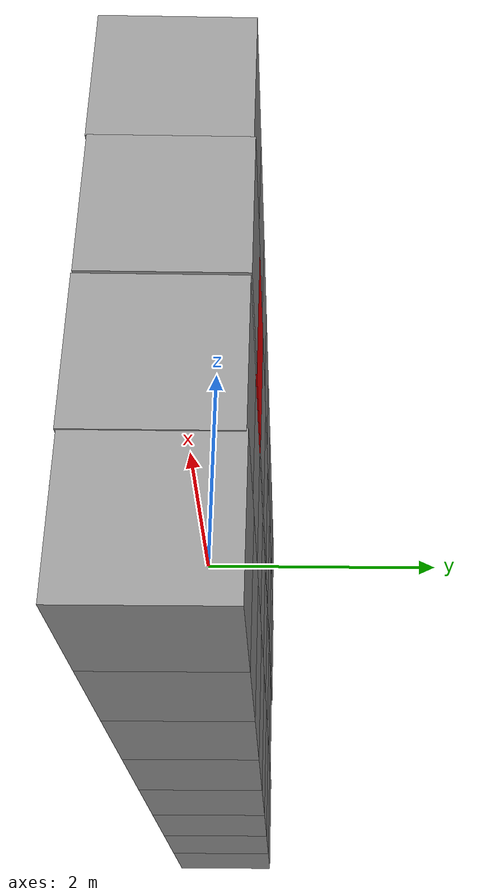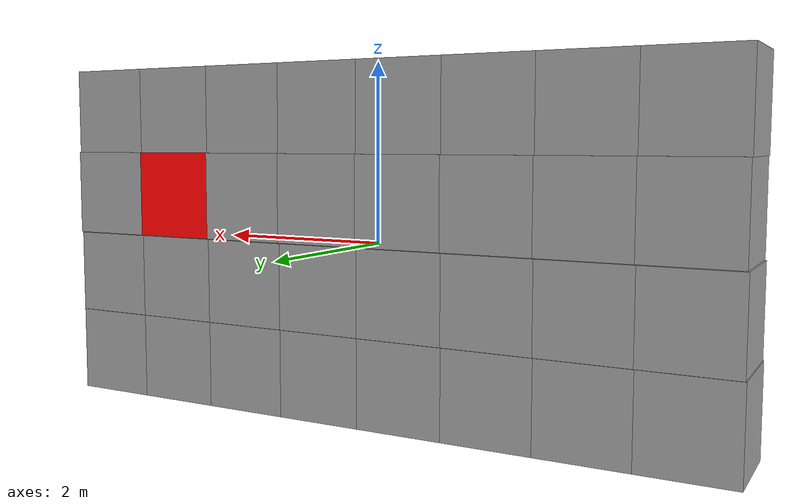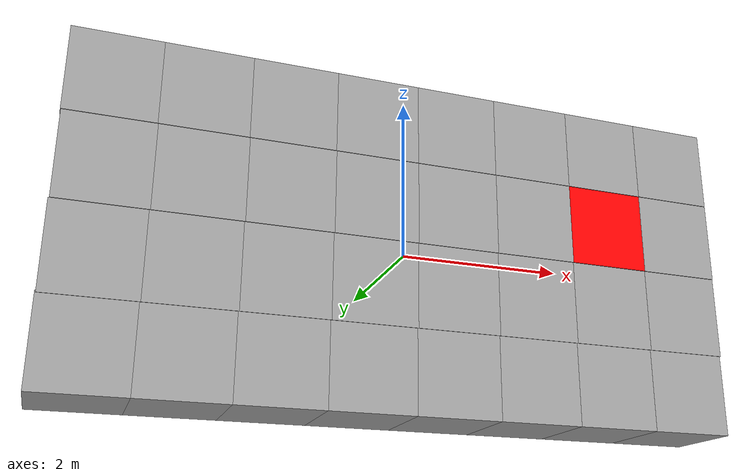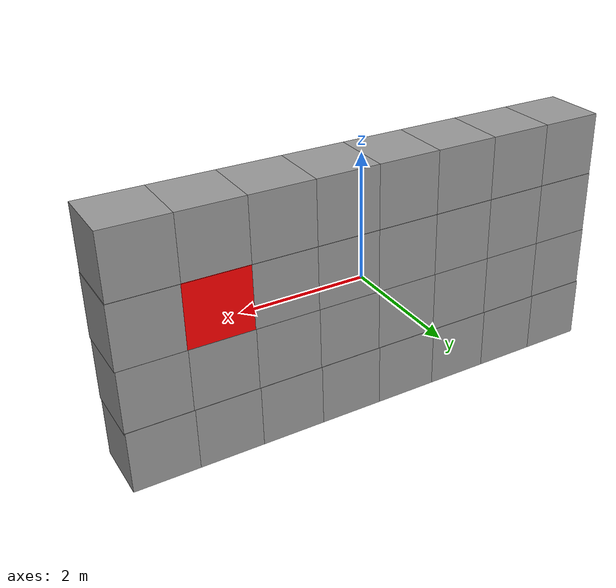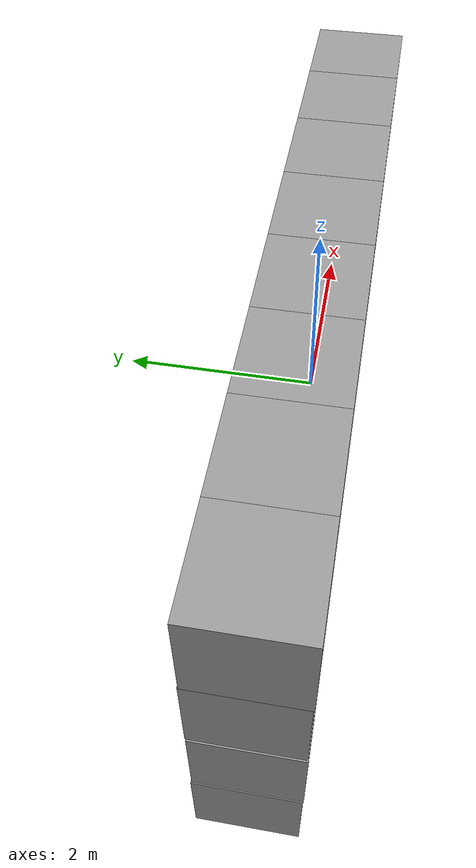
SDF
<?xml version='1.0'?>
<sdf version='1.6'>
  <model name='serial_blocks_wall'>
    <model name='seiral_blocks'>
      <link name='link_10'>
        <pose frame=''>2.5 0 0 0 -0 0</pose>
        <inertial>
          <mass>1</mass>
          <inertia>
            <ixx>0.166667</ixx>
            <ixy>0</ixy>
            <ixz>0</ixz>
            <iyy>0.166667</iyy>
            <iyz>0</iyz>
            <izz>0.166667</izz>
          </inertia>
          <pose frame=''>0 0 0 0 -0 0</pose>
        </inertial>
        <gravity>1</gravity>
        <self_collide>0</self_collide>
        <kinematic>0</kinematic>
        <visual name='visual'>
          <pose frame=''>0 0 0 0 -0 0</pose>
          <geometry>
            <box>
              <size>1 1 1</size>
            </box>
          </geometry>
          <material>
            <lighting>1</lighting>
            <script>
              <uri>file://media/materials/scripts/gazebo.material</uri>
              <name>Gazebo/Grey</name>
            </script>
            <shader type='pixel'>
              <normal_map>__default__</normal_map>
            </shader>
            <ambient>0.3 0.3 0.3 1</ambient>
            <diffuse>0.7 0.7 0.7 1</diffuse>
            <specular>0.01 0.01 0.01 1</specular>
            <emissive>0 0 0 1</emissive>
          </material>
          <transparency>0</transparency>
          <cast_shadows>1</cast_shadows>
        </visual>
        <collision name='collision'>
          <laser_retro>0</laser_retro>
          <max_contacts>10</max_contacts>
          <pose frame=''>0 0 0 0 -0 0</pose>
          <geometry>
            <box>
              <size>1 1 1</size>
            </box>
          </geometry>
          <surface>
            <friction>
              <ode>
                <mu>1</mu>
                <mu2>1</mu2>
                <fdir1>0 0 0</fdir1>
                <slip1>0</slip1>
                <slip2>0</slip2>
              </ode>
              <torsional>
                <coefficient>1</coefficient>
                <patch_radius>0</patch_radius>
                <surface_radius>0</surface_radius>
                <use_patch_radius>1</use_patch_radius>
                <ode>
                  <slip>0</slip>
                </ode>
              </torsional>
            </friction>
            <bounce>
              <restitution_coefficient>0</restitution_coefficient>
              <threshold>1e+06</threshold>
            </bounce>
            <contact>
              <collide_without_contact>0</collide_without_contact>
              <collide_without_contact_bitmask>1</collide_without_contact_bitmask>
              <collide_bitmask>1</collide_bitmask>
              <ode>
                <soft_cfm>0</soft_cfm>
                <soft_erp>0.2</soft_erp>
                <kp>1e+13</kp>
                <kd>1</kd>
                <max_vel>0.01</max_vel>
                <min_depth>0</min_depth>
              </ode>
              <bullet>
                <split_impulse>1</split_impulse>
                <split_impulse_penetration_threshold>-0.01</split_impulse_penetration_threshold>
                <soft_cfm>0</soft_cfm>
                <soft_erp>0.2</soft_erp>
                <kp>1e+13</kp>
                <kd>1</kd>
              </bullet>
            </contact>
          </surface>
        </collision>
      </link>
      <link name='link_11'>
        <pose frame=''>3.5 0 0 0 -0 0</pose>
        <inertial>
          <mass>1</mass>
          <inertia>
            <ixx>0.166667</ixx>
            <ixy>0</ixy>
            <ixz>0</ixz>
            <iyy>0.166667</iyy>
            <iyz>0</iyz>
            <izz>0.166667</izz>
          </inertia>
          <pose frame=''>0 0 0 0 -0 0</pose>
        </inertial>
        <gravity>1</gravity>
        <self_collide>0</self_collide>
        <kinematic>0</kinematic>
        <visual name='visual'>
          <pose frame=''>0 0 0 0 -0 0</pose>
          <geometry>
            <box>
              <size>1 1 1</size>
            </box>
          </geometry>
          <material>
            <lighting>1</lighting>
            <script>
              <uri>file://media/materials/scripts/gazebo.material</uri>
              <name>Gazebo/Grey</name>
            </script>
            <shader type='pixel'>
              <normal_map>__default__</normal_map>
            </shader>
            <ambient>0.3 0.3 0.3 1</ambient>
            <diffuse>0.7 0.7 0.7 1</diffuse>
            <specular>0.01 0.01 0.01 1</specular>
            <emissive>0 0 0 1</emissive>
          </material>
          <transparency>0</transparency>
          <cast_shadows>1</cast_shadows>
        </visual>
        <collision name='collision'>
          <laser_retro>0</laser_retro>
          <max_contacts>10</max_contacts>
          <pose frame=''>0 0 0 0 -0 0</pose>
          <geometry>
            <box>
              <size>1 1 1</size>
            </box>
          </geometry>
          <surface>
            <friction>
              <ode>
                <mu>1</mu>
                <mu2>1</mu2>
                <fdir1>0 0 0</fdir1>
                <slip1>0</slip1>
                <slip2>0</slip2>
              </ode>
              <torsional>
                <coefficient>1</coefficient>
                <patch_radius>0</patch_radius>
                <surface_radius>0</surface_radius>
                <use_patch_radius>1</use_patch_radius>
                <ode>
                  <slip>0</slip>
                </ode>
              </torsional>
            </friction>
            <bounce>
              <restitution_coefficient>0</restitution_coefficient>
              <threshold>1e+06</threshold>
            </bounce>
            <contact>
              <collide_without_contact>0</collide_without_contact>
              <collide_without_contact_bitmask>1</collide_without_contact_bitmask>
              <collide_bitmask>1</collide_bitmask>
              <ode>
                <soft_cfm>0</soft_cfm>
                <soft_erp>0.2</soft_erp>
                <kp>1e+13</kp>
                <kd>1</kd>
                <max_vel>0.01</max_vel>
                <min_depth>0</min_depth>
              </ode>
              <bullet>
                <split_impulse>1</split_impulse>
                <split_impulse_penetration_threshold>-0.01</split_impulse_penetration_threshold>
                <soft_cfm>0</soft_cfm>
                <soft_erp>0.2</soft_erp>
                <kp>1e+13</kp>
                <kd>1</kd>
              </bullet>
            </contact>
          </surface>
        </collision>
      </link>
      <link name='link_15'>
        <pose frame=''>-2.5 0 0 0 -0 0</pose>
        <inertial>
          <mass>1</mass>
          <inertia>
            <ixx>0.166667</ixx>
            <ixy>0</ixy>
            <ixz>0</ixz>
            <iyy>0.166667</iyy>
            <iyz>0</iyz>
            <izz>0.166667</izz>
          </inertia>
          <pose frame=''>0 0 0 0 -0 0</pose>
        </inertial>
        <gravity>1</gravity>
        <self_collide>0</self_collide>
        <kinematic>0</kinematic>
        <visual name='visual'>
          <pose frame=''>0 0 0 0 -0 0</pose>
          <geometry>
            <box>
              <size>1 1 1</size>
            </box>
          </geometry>
          <material>
            <lighting>1</lighting>
            <script>
              <uri>file://media/materials/scripts/gazebo.material</uri>
              <name>Gazebo/Grey</name>
            </script>
            <shader type='pixel'>
              <normal_map>__default__</normal_map>
            </shader>
            <ambient>0.3 0.3 0.3 1</ambient>
            <diffuse>0.7 0.7 0.7 1</diffuse>
            <specular>0.01 0.01 0.01 1</specular>
            <emissive>0 0 0 1</emissive>
          </material>
          <transparency>0</transparency>
          <cast_shadows>1</cast_shadows>
        </visual>
        <collision name='collision'>
          <laser_retro>0</laser_retro>
          <max_contacts>10</max_contacts>
          <pose frame=''>0 0 0 0 -0 0</pose>
          <geometry>
            <box>
              <size>1 1 1</size>
            </box>
          </geometry>
          <surface>
            <friction>
              <ode>
                <mu>1</mu>
                <mu2>1</mu2>
                <fdir1>0 0 0</fdir1>
                <slip1>0</slip1>
                <slip2>0</slip2>
              </ode>
              <torsional>
                <coefficient>1</coefficient>
                <patch_radius>0</patch_radius>
                <surface_radius>0</surface_radius>
                <use_patch_radius>1</use_patch_radius>
                <ode>
                  <slip>0</slip>
                </ode>
              </torsional>
            </friction>
            <bounce>
              <restitution_coefficient>0</restitution_coefficient>
              <threshold>1e+06</threshold>
            </bounce>
            <contact>
              <collide_without_contact>0</collide_without_contact>
              <collide_without_contact_bitmask>1</collide_without_contact_bitmask>
              <collide_bitmask>1</collide_bitmask>
              <ode>
                <soft_cfm>0</soft_cfm>
                <soft_erp>0.2</soft_erp>
                <kp>1e+13</kp>
                <kd>1</kd>
                <max_vel>0.01</max_vel>
                <min_depth>0</min_depth>
              </ode>
              <bullet>
                <split_impulse>1</split_impulse>
                <split_impulse_penetration_threshold>-0.01</split_impulse_penetration_threshold>
                <soft_cfm>0</soft_cfm>
                <soft_erp>0.2</soft_erp>
                <kp>1e+13</kp>
                <kd>1</kd>
              </bullet>
            </contact>
          </surface>
        </collision>
      </link>
      <link name='link_16'>
        <pose frame=''>-0.5 0 0 0 -0 0</pose>
        <inertial>
          <mass>1</mass>
          <inertia>
            <ixx>0.166667</ixx>
            <ixy>0</ixy>
            <ixz>0</ixz>
            <iyy>0.166667</iyy>
            <iyz>0</iyz>
            <izz>0.166667</izz>
          </inertia>
          <pose frame=''>0 0 0 0 -0 0</pose>
        </inertial>
        <gravity>1</gravity>
        <self_collide>0</self_collide>
        <kinematic>0</kinematic>
        <visual name='visual'>
          <pose frame=''>0 0 0 0 -0 0</pose>
          <geometry>
            <box>
              <size>1 1 1</size>
            </box>
          </geometry>
          <material>
            <lighting>1</lighting>
            <script>
              <uri>file://media/materials/scripts/gazebo.material</uri>
              <name>Gazebo/Grey</name>
            </script>
            <shader type='pixel'>
              <normal_map>__default__</normal_map>
            </shader>
            <ambient>0.3 0.3 0.3 1</ambient>
            <diffuse>0.7 0.7 0.7 1</diffuse>
            <specular>0.01 0.01 0.01 1</specular>
            <emissive>0 0 0 1</emissive>
          </material>
          <transparency>0</transparency>
          <cast_shadows>1</cast_shadows>
        </visual>
        <collision name='collision'>
          <laser_retro>0</laser_retro>
          <max_contacts>10</max_contacts>
          <pose frame=''>0 0 0 0 -0 0</pose>
          <geometry>
            <box>
              <size>1 1 1</size>
            </box>
          </geometry>
          <surface>
            <friction>
              <ode>
                <mu>1</mu>
                <mu2>1</mu2>
                <fdir1>0 0 0</fdir1>
                <slip1>0</slip1>
                <slip2>0</slip2>
              </ode>
              <torsional>
                <coefficient>1</coefficient>
                <patch_radius>0</patch_radius>
                <surface_radius>0</surface_radius>
                <use_patch_radius>1</use_patch_radius>
                <ode>
                  <slip>0</slip>
                </ode>
              </torsional>
            </friction>
            <bounce>
              <restitution_coefficient>0</restitution_coefficient>
              <threshold>1e+06</threshold>
            </bounce>
            <contact>
              <collide_without_contact>0</collide_without_contact>
              <collide_without_contact_bitmask>1</collide_without_contact_bitmask>
              <collide_bitmask>1</collide_bitmask>
              <ode>
                <soft_cfm>0</soft_cfm>
                <soft_erp>0.2</soft_erp>
                <kp>1e+13</kp>
                <kd>1</kd>
                <max_vel>0.01</max_vel>
                <min_depth>0</min_depth>
              </ode>
              <bullet>
                <split_impulse>1</split_impulse>
                <split_impulse_penetration_threshold>-0.01</split_impulse_penetration_threshold>
                <soft_cfm>0</soft_cfm>
                <soft_erp>0.2</soft_erp>
                <kp>1e+13</kp>
                <kd>1</kd>
              </bullet>
            </contact>
          </surface>
        </collision>
      </link>
      <link name='link_6'>
        <pose frame=''>-1.5 0 0 0 -0 0</pose>
        <inertial>
          <mass>1</mass>
          <inertia>
            <ixx>0.166667</ixx>
            <ixy>0</ixy>
            <ixz>0</ixz>
            <iyy>0.166667</iyy>
            <iyz>0</iyz>
            <izz>0.166667</izz>
          </inertia>
          <pose frame=''>0 0 0 0 -0 0</pose>
        </inertial>
        <gravity>1</gravity>
        <self_collide>0</self_collide>
        <kinematic>0</kinematic>
        <visual name='visual'>
          <pose frame=''>0 0 0 0 -0 0</pose>
          <geometry>
            <box>
              <size>1 1 1</size>
            </box>
          </geometry>
          <material>
            <lighting>1</lighting>
            <script>
              <uri>file://media/materials/scripts/gazebo.material</uri>
              <name>Gazebo/Grey</name>
            </script>
            <shader type='pixel'>
              <normal_map>__default__</normal_map>
            </shader>
            <ambient>0.3 0.3 0.3 1</ambient>
            <diffuse>0.7 0.7 0.7 1</diffuse>
            <specular>0.01 0.01 0.01 1</specular>
            <emissive>0 0 0 1</emissive>
          </material>
          <transparency>0</transparency>
          <cast_shadows>1</cast_shadows>
        </visual>
        <collision name='collision'>
          <laser_retro>0</laser_retro>
          <max_contacts>10</max_contacts>
          <pose frame=''>0 0 0 0 -0 0</pose>
          <geometry>
            <box>
              <size>1 1 1</size>
            </box>
          </geometry>
          <surface>
            <friction>
              <ode>
                <mu>1</mu>
                <mu2>1</mu2>
                <fdir1>0 0 0</fdir1>
                <slip1>0</slip1>
                <slip2>0</slip2>
              </ode>
              <torsional>
                <coefficient>1</coefficient>
                <patch_radius>0</patch_radius>
                <surface_radius>0</surface_radius>
                <use_patch_radius>1</use_patch_radius>
                <ode>
                  <slip>0</slip>
                </ode>
              </torsional>
            </friction>
            <bounce>
              <restitution_coefficient>0</restitution_coefficient>
              <threshold>1e+06</threshold>
            </bounce>
            <contact>
              <collide_without_contact>0</collide_without_contact>
              <collide_without_contact_bitmask>1</collide_without_contact_bitmask>
              <collide_bitmask>1</collide_bitmask>
              <ode>
                <soft_cfm>0</soft_cfm>
                <soft_erp>0.2</soft_erp>
                <kp>1e+13</kp>
                <kd>1</kd>
                <max_vel>0.01</max_vel>
                <min_depth>0</min_depth>
              </ode>
              <bullet>
                <split_impulse>1</split_impulse>
                <split_impulse_penetration_threshold>-0.01</split_impulse_penetration_threshold>
                <soft_cfm>0</soft_cfm>
                <soft_erp>0.2</soft_erp>
                <kp>1e+13</kp>
                <kd>1</kd>
              </bullet>
            </contact>
          </surface>
        </collision>
      </link>
      <link name='link_7'>
        <pose frame=''>-3.5 0 0 0 -0 0</pose>
        <inertial>
          <mass>1</mass>
          <inertia>
            <ixx>0.166667</ixx>
            <ixy>0</ixy>
            <ixz>0</ixz>
            <iyy>0.166667</iyy>
            <iyz>0</iyz>
            <izz>0.166667</izz>
          </inertia>
          <pose frame=''>0 0 0 0 -0 0</pose>
        </inertial>
        <gravity>1</gravity>
        <self_collide>0</self_collide>
        <kinematic>0</kinematic>
        <visual name='visual'>
          <pose frame=''>0 0 0 0 -0 0</pose>
          <geometry>
            <box>
              <size>1 1 1</size>
            </box>
          </geometry>
          <material>
            <lighting>1</lighting>
            <script>
              <uri>file://media/materials/scripts/gazebo.material</uri>
              <name>Gazebo/Grey</name>
            </script>
            <shader type='pixel'>
              <normal_map>__default__</normal_map>
            </shader>
            <ambient>0.3 0.3 0.3 1</ambient>
            <diffuse>0.7 0.7 0.7 1</diffuse>
            <specular>0.01 0.01 0.01 1</specular>
            <emissive>0 0 0 1</emissive>
          </material>
          <transparency>0</transparency>
          <cast_shadows>1</cast_shadows>
        </visual>
        <collision name='collision'>
          <laser_retro>0</laser_retro>
          <max_contacts>10</max_contacts>
          <pose frame=''>0 0 0 0 -0 0</pose>
          <geometry>
            <box>
              <size>1 1 1</size>
            </box>
          </geometry>
          <surface>
            <friction>
              <ode>
                <mu>1</mu>
                <mu2>1</mu2>
                <fdir1>0 0 0</fdir1>
                <slip1>0</slip1>
                <slip2>0</slip2>
              </ode>
              <torsional>
                <coefficient>1</coefficient>
                <patch_radius>0</patch_radius>
                <surface_radius>0</surface_radius>
                <use_patch_radius>1</use_patch_radius>
                <ode>
                  <slip>0</slip>
                </ode>
              </torsional>
            </friction>
            <bounce>
              <restitution_coefficient>0</restitution_coefficient>
              <threshold>1e+06</threshold>
            </bounce>
            <contact>
              <collide_without_contact>0</collide_without_contact>
              <collide_without_contact_bitmask>1</collide_without_contact_bitmask>
              <collide_bitmask>1</collide_bitmask>
              <ode>
                <soft_cfm>0</soft_cfm>
                <soft_erp>0.2</soft_erp>
                <kp>1e+13</kp>
                <kd>1</kd>
                <max_vel>0.01</max_vel>
                <min_depth>0</min_depth>
              </ode>
              <bullet>
                <split_impulse>1</split_impulse>
                <split_impulse_penetration_threshold>-0.01</split_impulse_penetration_threshold>
                <soft_cfm>0</soft_cfm>
                <soft_erp>0.2</soft_erp>
                <kp>1e+13</kp>
                <kd>1</kd>
              </bullet>
            </contact>
          </surface>
        </collision>
      </link>
      <link name='link_8'>
        <pose frame=''>0.5 0 0 0 -0 0</pose>
        <inertial>
          <mass>1</mass>
          <inertia>
            <ixx>0.166667</ixx>
            <ixy>0</ixy>
            <ixz>0</ixz>
            <iyy>0.166667</iyy>
            <iyz>0</iyz>
            <izz>0.166667</izz>
          </inertia>
          <pose frame=''>0 0 0 0 -0 0</pose>
        </inertial>
        <gravity>1</gravity>
        <self_collide>0</self_collide>
        <kinematic>0</kinematic>
        <visual name='visual'>
          <pose frame=''>0 0 0 0 -0 0</pose>
          <geometry>
            <box>
              <size>1 1 1</size>
            </box>
          </geometry>
          <material>
            <lighting>1</lighting>
            <script>
              <uri>file://media/materials/scripts/gazebo.material</uri>
              <name>Gazebo/Grey</name>
            </script>
            <shader type='pixel'>
              <normal_map>__default__</normal_map>
            </shader>
            <ambient>0.3 0.3 0.3 1</ambient>
            <diffuse>0.7 0.7 0.7 1</diffuse>
            <specular>0.01 0.01 0.01 1</specular>
            <emissive>0 0 0 1</emissive>
          </material>
          <transparency>0</transparency>
          <cast_shadows>1</cast_shadows>
        </visual>
        <collision name='collision'>
          <laser_retro>0</laser_retro>
          <max_contacts>10</max_contacts>
          <pose frame=''>0 0 0 0 -0 0</pose>
          <geometry>
            <box>
              <size>1 1 1</size>
            </box>
          </geometry>
          <surface>
            <friction>
              <ode>
                <mu>1</mu>
                <mu2>1</mu2>
                <fdir1>0 0 0</fdir1>
                <slip1>0</slip1>
                <slip2>0</slip2>
              </ode>
              <torsional>
                <coefficient>1</coefficient>
                <patch_radius>0</patch_radius>
                <surface_radius>0</surface_radius>
                <use_patch_radius>1</use_patch_radius>
                <ode>
                  <slip>0</slip>
                </ode>
              </torsional>
            </friction>
            <bounce>
              <restitution_coefficient>0</restitution_coefficient>
              <threshold>1e+06</threshold>
            </bounce>
            <contact>
              <collide_without_contact>0</collide_without_contact>
              <collide_without_contact_bitmask>1</collide_without_contact_bitmask>
              <collide_bitmask>1</collide_bitmask>
              <ode>
                <soft_cfm>0</soft_cfm>
                <soft_erp>0.2</soft_erp>
                <kp>1e+13</kp>
                <kd>1</kd>
                <max_vel>0.01</max_vel>
                <min_depth>0</min_depth>
              </ode>
              <bullet>
                <split_impulse>1</split_impulse>
                <split_impulse_penetration_threshold>-0.01</split_impulse_penetration_threshold>
                <soft_cfm>0</soft_cfm>
                <soft_erp>0.2</soft_erp>
                <kp>1e+13</kp>
                <kd>1</kd>
              </bullet>
            </contact>
          </surface>
        </collision>
      </link>
      <link name='link_9'>
        <pose frame=''>1.5 0 0 0 -0 0</pose>
        <inertial>
          <mass>1</mass>
          <inertia>
            <ixx>0.166667</ixx>
            <ixy>0</ixy>
            <ixz>0</ixz>
            <iyy>0.166667</iyy>
            <iyz>0</iyz>
            <izz>0.166667</izz>
          </inertia>
          <pose frame=''>0 0 0 0 -0 0</pose>
        </inertial>
        <gravity>1</gravity>
        <self_collide>0</self_collide>
        <kinematic>0</kinematic>
        <visual name='visual'>
          <pose frame=''>0 0 0 0 -0 0</pose>
          <geometry>
            <box>
              <size>1 1 1</size>
            </box>
          </geometry>
          <material>
            <lighting>1</lighting>
            <script>
              <uri>file://media/materials/scripts/gazebo.material</uri>
              <name>Gazebo/Grey</name>
            </script>
            <shader type='pixel'>
              <normal_map>__default__</normal_map>
            </shader>
            <ambient>0.3 0.3 0.3 1</ambient>
            <diffuse>0.7 0.7 0.7 1</diffuse>
            <specular>0.01 0.01 0.01 1</specular>
            <emissive>0 0 0 1</emissive>
          </material>
          <transparency>0</transparency>
          <cast_shadows>1</cast_shadows>
        </visual>
        <collision name='collision'>
          <laser_retro>0</laser_retro>
          <max_contacts>10</max_contacts>
          <pose frame=''>0 0 0 0 -0 0</pose>
          <geometry>
            <box>
              <size>1 1 1</size>
            </box>
          </geometry>
          <surface>
            <friction>
              <ode>
                <mu>1</mu>
                <mu2>1</mu2>
                <fdir1>0 0 0</fdir1>
                <slip1>0</slip1>
                <slip2>0</slip2>
              </ode>
              <torsional>
                <coefficient>1</coefficient>
                <patch_radius>0</patch_radius>
                <surface_radius>0</surface_radius>
                <use_patch_radius>1</use_patch_radius>
                <ode>
                  <slip>0</slip>
                </ode>
              </torsional>
            </friction>
            <bounce>
              <restitution_coefficient>0</restitution_coefficient>
              <threshold>1e+06</threshold>
            </bounce>
            <contact>
              <collide_without_contact>0</collide_without_contact>
              <collide_without_contact_bitmask>1</collide_without_contact_bitmask>
              <collide_bitmask>1</collide_bitmask>
              <ode>
                <soft_cfm>0</soft_cfm>
                <soft_erp>0.2</soft_erp>
                <kp>1e+13</kp>
                <kd>1</kd>
                <max_vel>0.01</max_vel>
                <min_depth>0</min_depth>
              </ode>
              <bullet>
                <split_impulse>1</split_impulse>
                <split_impulse_penetration_threshold>-0.01</split_impulse_penetration_threshold>
                <soft_cfm>0</soft_cfm>
                <soft_erp>0.2</soft_erp>
                <kp>1e+13</kp>
                <kd>1</kd>
              </bullet>
            </contact>
          </surface>
        </collision>
      </link>
      <joint name='link_10_JOINT_10' type='fixed'>
        <parent>link_10</parent>
        <child>link_11</child>
        <pose frame=''>0 0 0 0 -0 0</pose>
        <physics>
          <ode>
            <limit>
              <cfm>0</cfm>
              <erp>0.2</erp>
            </limit>
            <suspension>
              <cfm>0</cfm>
              <erp>0.2</erp>
            </suspension>
          </ode>
        </physics>
      </joint>
      <joint name='link_15_JOINT_5' type='fixed'>
        <parent>link_15</parent>
        <child>link_6</child>
        <pose frame=''>0 0 0 0 -0 0</pose>
        <physics>
          <ode>
            <limit>
              <cfm>0</cfm>
              <erp>0.2</erp>
            </limit>
            <suspension>
              <cfm>0</cfm>
              <erp>0.2</erp>
            </suspension>
          </ode>
        </physics>
      </joint>
      <joint name='link_16_JOINT_7' type='fixed'>
        <parent>link_16</parent>
        <child>link_8</child>
        <pose frame=''>0 0 0 0 -0 0</pose>
        <physics>
          <ode>
            <limit>
              <cfm>0</cfm>
              <erp>0.2</erp>
            </limit>
            <suspension>
              <cfm>0</cfm>
              <erp>0.2</erp>
            </suspension>
          </ode>
        </physics>
      </joint>
      <joint name='link_6_JOINT_6' type='fixed'>
        <parent>link_6</parent>
        <child>link_16</child>
        <pose frame=''>0 0 0 0 -0 0</pose>
        <physics>
          <ode>
            <limit>
              <cfm>0</cfm>
              <erp>0.2</erp>
            </limit>
            <suspension>
              <cfm>0</cfm>
              <erp>0.2</erp>
            </suspension>
          </ode>
        </physics>
      </joint>
      <joint name='link_7_JOINT_4' type='fixed'>
        <parent>link_7</parent>
        <child>link_15</child>
        <pose frame=''>0 0 0 0 -0 0</pose>
        <physics>
          <ode>
            <limit>
              <cfm>0</cfm>
              <erp>0.2</erp>
            </limit>
            <suspension>
              <cfm>0</cfm>
              <erp>0.2</erp>
            </suspension>
          </ode>
        </physics>
      </joint>
      <joint name='link_8_JOINT_8' type='fixed'>
        <parent>link_8</parent>
        <child>link_9</child>
        <pose frame=''>0 0 0 0 -0 0</pose>
        <physics>
          <ode>
            <limit>
              <cfm>0</cfm>
              <erp>0.2</erp>
            </limit>
            <suspension>
              <cfm>0</cfm>
              <erp>0.2</erp>
            </suspension>
          </ode>
        </physics>
      </joint>
      <joint name='link_9_JOINT_9' type='fixed'>
        <parent>link_9</parent>
        <child>link_10</child>
        <pose frame=''>0 0 0 0 -0 0</pose>
        <physics>
          <ode>
            <limit>
              <cfm>0</cfm>
              <erp>0.2</erp>
            </limit>
            <suspension>
              <cfm>0</cfm>
              <erp>0.2</erp>
            </suspension>
          </ode>
        </physics>
      </joint>
      <static>0</static>
      <allow_auto_disable>1</allow_auto_disable>
      <pose frame=''>-0.011667 0.005415 -1.48703 0 -0 0</pose>
    </model>
    <model name='seiral_blocks_0'>
      <link name='link_10'>
        <pose frame=''>2.5 0 0 0 -0 0</pose>
        <inertial>
          <mass>1</mass>
          <inertia>
            <ixx>0.166667</ixx>
            <ixy>0</ixy>
            <ixz>0</ixz>
            <iyy>0.166667</iyy>
            <iyz>0</iyz>
            <izz>0.166667</izz>
          </inertia>
          <pose frame=''>0 0 0 0 -0 0</pose>
        </inertial>
        <gravity>1</gravity>
        <self_collide>0</self_collide>
        <kinematic>0</kinematic>
        <visual name='visual'>
          <pose frame=''>0 0 0 0 -0 0</pose>
          <geometry>
            <box>
              <size>1 1 1</size>
            </box>
          </geometry>
          <material>
            <lighting>1</lighting>
            <script>
              <uri>file://media/materials/scripts/gazebo.material</uri>
              <name>Gazebo/Grey</name>
            </script>
            <shader type='pixel'>
              <normal_map>__default__</normal_map>
            </shader>
            <ambient>0.3 0.3 0.3 1</ambient>
            <diffuse>0.7 0.7 0.7 1</diffuse>
            <specular>0.01 0.01 0.01 1</specular>
            <emissive>0 0 0 1</emissive>
          </material>
          <transparency>0</transparency>
          <cast_shadows>1</cast_shadows>
        </visual>
        <collision name='collision'>
          <laser_retro>0</laser_retro>
          <max_contacts>10</max_contacts>
          <pose frame=''>0 0 0 0 -0 0</pose>
          <geometry>
            <box>
              <size>1 1 1</size>
            </box>
          </geometry>
          <surface>
            <friction>
              <ode>
                <mu>1</mu>
                <mu2>1</mu2>
                <fdir1>0 0 0</fdir1>
                <slip1>0</slip1>
                <slip2>0</slip2>
              </ode>
              <torsional>
                <coefficient>1</coefficient>
                <patch_radius>0</patch_radius>
                <surface_radius>0</surface_radius>
                <use_patch_radius>1</use_patch_radius>
                <ode>
                  <slip>0</slip>
                </ode>
              </torsional>
            </friction>
            <bounce>
              <restitution_coefficient>0</restitution_coefficient>
              <threshold>1e+06</threshold>
            </bounce>
            <contact>
              <collide_without_contact>0</collide_without_contact>
              <collide_without_contact_bitmask>1</collide_without_contact_bitmask>
              <collide_bitmask>1</collide_bitmask>
              <ode>
                <soft_cfm>0</soft_cfm>
                <soft_erp>0.2</soft_erp>
                <kp>1e+13</kp>
                <kd>1</kd>
                <max_vel>0.01</max_vel>
                <min_depth>0</min_depth>
              </ode>
              <bullet>
                <split_impulse>1</split_impulse>
                <split_impulse_penetration_threshold>-0.01</split_impulse_penetration_threshold>
                <soft_cfm>0</soft_cfm>
                <soft_erp>0.2</soft_erp>
                <kp>1e+13</kp>
                <kd>1</kd>
              </bullet>
            </contact>
          </surface>
        </collision>
      </link>
      <link name='link_11'>
        <pose frame=''>3.5 0 0 0 -0 0</pose>
        <inertial>
          <mass>1</mass>
          <inertia>
            <ixx>0.166667</ixx>
            <ixy>0</ixy>
            <ixz>0</ixz>
            <iyy>0.166667</iyy>
            <iyz>0</iyz>
            <izz>0.166667</izz>
          </inertia>
          <pose frame=''>0 0 0 0 -0 0</pose>
        </inertial>
        <gravity>1</gravity>
        <self_collide>0</self_collide>
        <kinematic>0</kinematic>
        <visual name='visual'>
          <pose frame=''>0 0 0 0 -0 0</pose>
          <geometry>
            <box>
              <size>1 1 1</size>
            </box>
          </geometry>
          <material>
            <lighting>1</lighting>
            <script>
              <uri>file://media/materials/scripts/gazebo.material</uri>
              <name>Gazebo/Grey</name>
            </script>
            <shader type='pixel'>
              <normal_map>__default__</normal_map>
            </shader>
            <ambient>0.3 0.3 0.3 1</ambient>
            <diffuse>0.7 0.7 0.7 1</diffuse>
            <specular>0.01 0.01 0.01 1</specular>
            <emissive>0 0 0 1</emissive>
          </material>
          <transparency>0</transparency>
          <cast_shadows>1</cast_shadows>
        </visual>
        <collision name='collision'>
          <laser_retro>0</laser_retro>
          <max_contacts>10</max_contacts>
          <pose frame=''>0 0 0 0 -0 0</pose>
          <geometry>
            <box>
              <size>1 1 1</size>
            </box>
          </geometry>
          <surface>
            <friction>
              <ode>
                <mu>1</mu>
                <mu2>1</mu2>
                <fdir1>0 0 0</fdir1>
                <slip1>0</slip1>
                <slip2>0</slip2>
              </ode>
              <torsional>
                <coefficient>1</coefficient>
                <patch_radius>0</patch_radius>
                <surface_radius>0</surface_radius>
                <use_patch_radius>1</use_patch_radius>
                <ode>
                  <slip>0</slip>
                </ode>
              </torsional>
            </friction>
            <bounce>
              <restitution_coefficient>0</restitution_coefficient>
              <threshold>1e+06</threshold>
            </bounce>
            <contact>
              <collide_without_contact>0</collide_without_contact>
              <collide_without_contact_bitmask>1</collide_without_contact_bitmask>
              <collide_bitmask>1</collide_bitmask>
              <ode>
                <soft_cfm>0</soft_cfm>
                <soft_erp>0.2</soft_erp>
                <kp>1e+13</kp>
                <kd>1</kd>
                <max_vel>0.01</max_vel>
                <min_depth>0</min_depth>
              </ode>
              <bullet>
                <split_impulse>1</split_impulse>
                <split_impulse_penetration_threshold>-0.01</split_impulse_penetration_threshold>
                <soft_cfm>0</soft_cfm>
                <soft_erp>0.2</soft_erp>
                <kp>1e+13</kp>
                <kd>1</kd>
              </bullet>
            </contact>
          </surface>
        </collision>
      </link>
      <link name='link_15'>
        <pose frame=''>-2.5 0 0 0 -0 0</pose>
        <inertial>
          <mass>1</mass>
          <inertia>
            <ixx>0.166667</ixx>
            <ixy>0</ixy>
            <ixz>0</ixz>
            <iyy>0.166667</iyy>
            <iyz>0</iyz>
            <izz>0.166667</izz>
          </inertia>
          <pose frame=''>0 0 0 0 -0 0</pose>
        </inertial>
        <gravity>1</gravity>
        <self_collide>0</self_collide>
        <kinematic>0</kinematic>
        <visual name='visual'>
          <pose frame=''>0 0 0 0 -0 0</pose>
          <geometry>
            <box>
              <size>1 1 1</size>
            </box>
          </geometry>
          <material>
            <lighting>1</lighting>
            <script>
              <uri>file://media/materials/scripts/gazebo.material</uri>
              <name>Gazebo/Grey</name>
            </script>
            <shader type='pixel'>
              <normal_map>__default__</normal_map>
            </shader>
            <ambient>0.3 0.3 0.3 1</ambient>
            <diffuse>0.7 0.7 0.7 1</diffuse>
            <specular>0.01 0.01 0.01 1</specular>
            <emissive>0 0 0 1</emissive>
          </material>
          <transparency>0</transparency>
          <cast_shadows>1</cast_shadows>
        </visual>
        <collision name='collision'>
          <laser_retro>0</laser_retro>
          <max_contacts>10</max_contacts>
          <pose frame=''>0 0 0 0 -0 0</pose>
          <geometry>
            <box>
              <size>1 1 1</size>
            </box>
          </geometry>
          <surface>
            <friction>
              <ode>
                <mu>1</mu>
                <mu2>1</mu2>
                <fdir1>0 0 0</fdir1>
                <slip1>0</slip1>
                <slip2>0</slip2>
              </ode>
              <torsional>
                <coefficient>1</coefficient>
                <patch_radius>0</patch_radius>
                <surface_radius>0</surface_radius>
                <use_patch_radius>1</use_patch_radius>
                <ode>
                  <slip>0</slip>
                </ode>
              </torsional>
            </friction>
            <bounce>
              <restitution_coefficient>0</restitution_coefficient>
              <threshold>1e+06</threshold>
            </bounce>
            <contact>
              <collide_without_contact>0</collide_without_contact>
              <collide_without_contact_bitmask>1</collide_without_contact_bitmask>
              <collide_bitmask>1</collide_bitmask>
              <ode>
                <soft_cfm>0</soft_cfm>
                <soft_erp>0.2</soft_erp>
                <kp>1e+13</kp>
                <kd>1</kd>
                <max_vel>0.01</max_vel>
                <min_depth>0</min_depth>
              </ode>
              <bullet>
                <split_impulse>1</split_impulse>
                <split_impulse_penetration_threshold>-0.01</split_impulse_penetration_threshold>
                <soft_cfm>0</soft_cfm>
                <soft_erp>0.2</soft_erp>
                <kp>1e+13</kp>
                <kd>1</kd>
              </bullet>
            </contact>
          </surface>
        </collision>
      </link>
      <link name='link_16'>
        <pose frame=''>-0.5 0 0 0 -0 0</pose>
        <inertial>
          <mass>1</mass>
          <inertia>
            <ixx>0.166667</ixx>
            <ixy>0</ixy>
            <ixz>0</ixz>
            <iyy>0.166667</iyy>
            <iyz>0</iyz>
            <izz>0.166667</izz>
          </inertia>
          <pose frame=''>0 0 0 0 -0 0</pose>
        </inertial>
        <gravity>1</gravity>
        <self_collide>0</self_collide>
        <kinematic>0</kinematic>
        <visual name='visual'>
          <pose frame=''>0 0 0 0 -0 0</pose>
          <geometry>
            <box>
              <size>1 1 1</size>
            </box>
          </geometry>
          <material>
            <lighting>1</lighting>
            <script>
              <uri>file://media/materials/scripts/gazebo.material</uri>
              <name>Gazebo/Grey</name>
            </script>
            <shader type='pixel'>
              <normal_map>__default__</normal_map>
            </shader>
            <ambient>0.3 0.3 0.3 1</ambient>
            <diffuse>0.7 0.7 0.7 1</diffuse>
            <specular>0.01 0.01 0.01 1</specular>
            <emissive>0 0 0 1</emissive>
          </material>
          <transparency>0</transparency>
          <cast_shadows>1</cast_shadows>
        </visual>
        <collision name='collision'>
          <laser_retro>0</laser_retro>
          <max_contacts>10</max_contacts>
          <pose frame=''>0 0 0 0 -0 0</pose>
          <geometry>
            <box>
              <size>1 1 1</size>
            </box>
          </geometry>
          <surface>
            <friction>
              <ode>
                <mu>1</mu>
                <mu2>1</mu2>
                <fdir1>0 0 0</fdir1>
                <slip1>0</slip1>
                <slip2>0</slip2>
              </ode>
              <torsional>
                <coefficient>1</coefficient>
                <patch_radius>0</patch_radius>
                <surface_radius>0</surface_radius>
                <use_patch_radius>1</use_patch_radius>
                <ode>
                  <slip>0</slip>
                </ode>
              </torsional>
            </friction>
            <bounce>
              <restitution_coefficient>0</restitution_coefficient>
              <threshold>1e+06</threshold>
            </bounce>
            <contact>
              <collide_without_contact>0</collide_without_contact>
              <collide_without_contact_bitmask>1</collide_without_contact_bitmask>
              <collide_bitmask>1</collide_bitmask>
              <ode>
                <soft_cfm>0</soft_cfm>
                <soft_erp>0.2</soft_erp>
                <kp>1e+13</kp>
                <kd>1</kd>
                <max_vel>0.01</max_vel>
                <min_depth>0</min_depth>
              </ode>
              <bullet>
                <split_impulse>1</split_impulse>
                <split_impulse_penetration_threshold>-0.01</split_impulse_penetration_threshold>
                <soft_cfm>0</soft_cfm>
                <soft_erp>0.2</soft_erp>
                <kp>1e+13</kp>
                <kd>1</kd>
              </bullet>
            </contact>
          </surface>
        </collision>
      </link>
      <link name='link_6'>
        <pose frame=''>-1.5 0 0 0 -0 0</pose>
        <inertial>
          <mass>1</mass>
          <inertia>
            <ixx>0.166667</ixx>
            <ixy>0</ixy>
            <ixz>0</ixz>
            <iyy>0.166667</iyy>
            <iyz>0</iyz>
            <izz>0.166667</izz>
          </inertia>
          <pose frame=''>0 0 0 0 -0 0</pose>
        </inertial>
        <gravity>1</gravity>
        <self_collide>0</self_collide>
        <kinematic>0</kinematic>
        <visual name='visual'>
          <pose frame=''>0 0 0 0 -0 0</pose>
          <geometry>
            <box>
              <size>1 1 1</size>
            </box>
          </geometry>
          <material>
            <lighting>1</lighting>
            <script>
              <uri>file://media/materials/scripts/gazebo.material</uri>
              <name>Gazebo/Grey</name>
            </script>
            <shader type='pixel'>
              <normal_map>__default__</normal_map>
            </shader>
            <ambient>0.3 0.3 0.3 1</ambient>
            <diffuse>0.7 0.7 0.7 1</diffuse>
            <specular>0.01 0.01 0.01 1</specular>
            <emissive>0 0 0 1</emissive>
          </material>
          <transparency>0</transparency>
          <cast_shadows>1</cast_shadows>
        </visual>
        <collision name='collision'>
          <laser_retro>0</laser_retro>
          <max_contacts>10</max_contacts>
          <pose frame=''>0 0 0 0 -0 0</pose>
          <geometry>
            <box>
              <size>1 1 1</size>
            </box>
          </geometry>
          <surface>
            <friction>
              <ode>
                <mu>1</mu>
                <mu2>1</mu2>
                <fdir1>0 0 0</fdir1>
                <slip1>0</slip1>
                <slip2>0</slip2>
              </ode>
              <torsional>
                <coefficient>1</coefficient>
                <patch_radius>0</patch_radius>
                <surface_radius>0</surface_radius>
                <use_patch_radius>1</use_patch_radius>
                <ode>
                  <slip>0</slip>
                </ode>
              </torsional>
            </friction>
            <bounce>
              <restitution_coefficient>0</restitution_coefficient>
              <threshold>1e+06</threshold>
            </bounce>
            <contact>
              <collide_without_contact>0</collide_without_contact>
              <collide_without_contact_bitmask>1</collide_without_contact_bitmask>
              <collide_bitmask>1</collide_bitmask>
              <ode>
                <soft_cfm>0</soft_cfm>
                <soft_erp>0.2</soft_erp>
                <kp>1e+13</kp>
                <kd>1</kd>
                <max_vel>0.01</max_vel>
                <min_depth>0</min_depth>
              </ode>
              <bullet>
                <split_impulse>1</split_impulse>
                <split_impulse_penetration_threshold>-0.01</split_impulse_penetration_threshold>
                <soft_cfm>0</soft_cfm>
                <soft_erp>0.2</soft_erp>
                <kp>1e+13</kp>
                <kd>1</kd>
              </bullet>
            </contact>
          </surface>
        </collision>
      </link>
      <link name='link_7'>
        <pose frame=''>-3.5 0 0 0 -0 0</pose>
        <inertial>
          <mass>1</mass>
          <inertia>
            <ixx>0.166667</ixx>
            <ixy>0</ixy>
            <ixz>0</ixz>
            <iyy>0.166667</iyy>
            <iyz>0</iyz>
            <izz>0.166667</izz>
          </inertia>
          <pose frame=''>0 0 0 0 -0 0</pose>
        </inertial>
        <gravity>1</gravity>
        <self_collide>0</self_collide>
        <kinematic>0</kinematic>
        <visual name='visual'>
          <pose frame=''>0 0 0 0 -0 0</pose>
          <geometry>
            <box>
              <size>1 1 1</size>
            </box>
          </geometry>
          <material>
            <lighting>1</lighting>
            <script>
              <uri>file://media/materials/scripts/gazebo.material</uri>
              <name>Gazebo/Grey</name>
            </script>
            <shader type='pixel'>
              <normal_map>__default__</normal_map>
            </shader>
            <ambient>0.3 0.3 0.3 1</ambient>
            <diffuse>0.7 0.7 0.7 1</diffuse>
            <specular>0.01 0.01 0.01 1</specular>
            <emissive>0 0 0 1</emissive>
          </material>
          <transparency>0</transparency>
          <cast_shadows>1</cast_shadows>
        </visual>
        <collision name='collision'>
          <laser_retro>0</laser_retro>
          <max_contacts>10</max_contacts>
          <pose frame=''>0 0 0 0 -0 0</pose>
          <geometry>
            <box>
              <size>1 1 1</size>
            </box>
          </geometry>
          <surface>
            <friction>
              <ode>
                <mu>1</mu>
                <mu2>1</mu2>
                <fdir1>0 0 0</fdir1>
                <slip1>0</slip1>
                <slip2>0</slip2>
              </ode>
              <torsional>
                <coefficient>1</coefficient>
                <patch_radius>0</patch_radius>
                <surface_radius>0</surface_radius>
                <use_patch_radius>1</use_patch_radius>
                <ode>
                  <slip>0</slip>
                </ode>
              </torsional>
            </friction>
            <bounce>
              <restitution_coefficient>0</restitution_coefficient>
              <threshold>1e+06</threshold>
            </bounce>
            <contact>
              <collide_without_contact>0</collide_without_contact>
              <collide_without_contact_bitmask>1</collide_without_contact_bitmask>
              <collide_bitmask>1</collide_bitmask>
              <ode>
                <soft_cfm>0</soft_cfm>
                <soft_erp>0.2</soft_erp>
                <kp>1e+13</kp>
                <kd>1</kd>
                <max_vel>0.01</max_vel>
                <min_depth>0</min_depth>
              </ode>
              <bullet>
                <split_impulse>1</split_impulse>
                <split_impulse_penetration_threshold>-0.01</split_impulse_penetration_threshold>
                <soft_cfm>0</soft_cfm>
                <soft_erp>0.2</soft_erp>
                <kp>1e+13</kp>
                <kd>1</kd>
              </bullet>
            </contact>
          </surface>
        </collision>
      </link>
      <link name='link_8'>
        <pose frame=''>0.5 0 0 0 -0 0</pose>
        <inertial>
          <mass>1</mass>
          <inertia>
            <ixx>0.166667</ixx>
            <ixy>0</ixy>
            <ixz>0</ixz>
            <iyy>0.166667</iyy>
            <iyz>0</iyz>
            <izz>0.166667</izz>
          </inertia>
          <pose frame=''>0 0 0 0 -0 0</pose>
        </inertial>
        <gravity>1</gravity>
        <self_collide>0</self_collide>
        <kinematic>0</kinematic>
        <visual name='visual'>
          <pose frame=''>0 0 0 0 -0 0</pose>
          <geometry>
            <box>
              <size>1 1 1</size>
            </box>
          </geometry>
          <material>
            <lighting>1</lighting>
            <script>
              <uri>file://media/materials/scripts/gazebo.material</uri>
              <name>Gazebo/Grey</name>
            </script>
            <shader type='pixel'>
              <normal_map>__default__</normal_map>
            </shader>
            <ambient>0.3 0.3 0.3 1</ambient>
            <diffuse>0.7 0.7 0.7 1</diffuse>
            <specular>0.01 0.01 0.01 1</specular>
            <emissive>0 0 0 1</emissive>
          </material>
          <transparency>0</transparency>
          <cast_shadows>1</cast_shadows>
        </visual>
        <collision name='collision'>
          <laser_retro>0</laser_retro>
          <max_contacts>10</max_contacts>
          <pose frame=''>0 0 0 0 -0 0</pose>
          <geometry>
            <box>
              <size>1 1 1</size>
            </box>
          </geometry>
          <surface>
            <friction>
              <ode>
                <mu>1</mu>
                <mu2>1</mu2>
                <fdir1>0 0 0</fdir1>
                <slip1>0</slip1>
                <slip2>0</slip2>
              </ode>
              <torsional>
                <coefficient>1</coefficient>
                <patch_radius>0</patch_radius>
                <surface_radius>0</surface_radius>
                <use_patch_radius>1</use_patch_radius>
                <ode>
                  <slip>0</slip>
                </ode>
              </torsional>
            </friction>
            <bounce>
              <restitution_coefficient>0</restitution_coefficient>
              <threshold>1e+06</threshold>
            </bounce>
            <contact>
              <collide_without_contact>0</collide_without_contact>
              <collide_without_contact_bitmask>1</collide_without_contact_bitmask>
              <collide_bitmask>1</collide_bitmask>
              <ode>
                <soft_cfm>0</soft_cfm>
                <soft_erp>0.2</soft_erp>
                <kp>1e+13</kp>
                <kd>1</kd>
                <max_vel>0.01</max_vel>
                <min_depth>0</min_depth>
              </ode>
              <bullet>
                <split_impulse>1</split_impulse>
                <split_impulse_penetration_threshold>-0.01</split_impulse_penetration_threshold>
                <soft_cfm>0</soft_cfm>
                <soft_erp>0.2</soft_erp>
                <kp>1e+13</kp>
                <kd>1</kd>
              </bullet>
            </contact>
          </surface>
        </collision>
      </link>
      <link name='link_9'>
        <pose frame=''>1.5 0 0 0 -0 0</pose>
        <inertial>
          <mass>1</mass>
          <inertia>
            <ixx>0.166667</ixx>
            <ixy>0</ixy>
            <ixz>0</ixz>
            <iyy>0.166667</iyy>
            <iyz>0</iyz>
            <izz>0.166667</izz>
          </inertia>
          <pose frame=''>0 0 0 0 -0 0</pose>
        </inertial>
        <gravity>1</gravity>
        <self_collide>0</self_collide>
        <kinematic>0</kinematic>
        <visual name='visual'>
          <pose frame=''>0 0 0 0 -0 0</pose>
          <geometry>
            <box>
              <size>1 1 1</size>
            </box>
          </geometry>
          <material>
            <lighting>1</lighting>
            <script>
              <uri>file://media/materials/scripts/gazebo.material</uri>
              <name>Gazebo/Grey</name>
            </script>
            <shader type='pixel'>
              <normal_map>__default__</normal_map>
            </shader>
            <ambient>0.3 0.3 0.3 1</ambient>
            <diffuse>0.7 0.7 0.7 1</diffuse>
            <specular>0.01 0.01 0.01 1</specular>
            <emissive>0 0 0 1</emissive>
          </material>
          <transparency>0</transparency>
          <cast_shadows>1</cast_shadows>
        </visual>
        <collision name='collision'>
          <laser_retro>0</laser_retro>
          <max_contacts>10</max_contacts>
          <pose frame=''>0 0 0 0 -0 0</pose>
          <geometry>
            <box>
              <size>1 1 1</size>
            </box>
          </geometry>
          <surface>
            <friction>
              <ode>
                <mu>1</mu>
                <mu2>1</mu2>
                <fdir1>0 0 0</fdir1>
                <slip1>0</slip1>
                <slip2>0</slip2>
              </ode>
              <torsional>
                <coefficient>1</coefficient>
                <patch_radius>0</patch_radius>
                <surface_radius>0</surface_radius>
                <use_patch_radius>1</use_patch_radius>
                <ode>
                  <slip>0</slip>
                </ode>
              </torsional>
            </friction>
            <bounce>
              <restitution_coefficient>0</restitution_coefficient>
              <threshold>1e+06</threshold>
            </bounce>
            <contact>
              <collide_without_contact>0</collide_without_contact>
              <collide_without_contact_bitmask>1</collide_without_contact_bitmask>
              <collide_bitmask>1</collide_bitmask>
              <ode>
                <soft_cfm>0</soft_cfm>
                <soft_erp>0.2</soft_erp>
                <kp>1e+13</kp>
                <kd>1</kd>
                <max_vel>0.01</max_vel>
                <min_depth>0</min_depth>
              </ode>
              <bullet>
                <split_impulse>1</split_impulse>
                <split_impulse_penetration_threshold>-0.01</split_impulse_penetration_threshold>
                <soft_cfm>0</soft_cfm>
                <soft_erp>0.2</soft_erp>
                <kp>1e+13</kp>
                <kd>1</kd>
              </bullet>
            </contact>
          </surface>
        </collision>
      </link>
      <joint name='link_10_JOINT_10' type='fixed'>
        <parent>link_10</parent>
        <child>link_11</child>
        <pose frame=''>0 0 0 0 -0 0</pose>
        <physics>
          <ode>
            <limit>
              <cfm>0</cfm>
              <erp>0.2</erp>
            </limit>
            <suspension>
              <cfm>0</cfm>
              <erp>0.2</erp>
            </suspension>
          </ode>
        </physics>
      </joint>
      <joint name='link_15_JOINT_5' type='fixed'>
        <parent>link_15</parent>
        <child>link_6</child>
        <pose frame=''>0 0 0 0 -0 0</pose>
        <physics>
          <ode>
            <limit>
              <cfm>0</cfm>
              <erp>0.2</erp>
            </limit>
            <suspension>
              <cfm>0</cfm>
              <erp>0.2</erp>
            </suspension>
          </ode>
        </physics>
      </joint>
      <joint name='link_16_JOINT_7' type='fixed'>
        <parent>link_16</parent>
        <child>link_8</child>
        <pose frame=''>0 0 0 0 -0 0</pose>
        <physics>
          <ode>
            <limit>
              <cfm>0</cfm>
              <erp>0.2</erp>
            </limit>
            <suspension>
              <cfm>0</cfm>
              <erp>0.2</erp>
            </suspension>
          </ode>
        </physics>
      </joint>
      <joint name='link_6_JOINT_6' type='fixed'>
        <parent>link_6</parent>
        <child>link_16</child>
        <pose frame=''>0 0 0 0 -0 0</pose>
        <physics>
          <ode>
            <limit>
              <cfm>0</cfm>
              <erp>0.2</erp>
            </limit>
            <suspension>
              <cfm>0</cfm>
              <erp>0.2</erp>
            </suspension>
          </ode>
        </physics>
      </joint>
      <joint name='link_7_JOINT_4' type='fixed'>
        <parent>link_7</parent>
        <child>link_15</child>
        <pose frame=''>0 0 0 0 -0 0</pose>
        <physics>
          <ode>
            <limit>
              <cfm>0</cfm>
              <erp>0.2</erp>
            </limit>
            <suspension>
              <cfm>0</cfm>
              <erp>0.2</erp>
            </suspension>
          </ode>
        </physics>
      </joint>
      <joint name='link_8_JOINT_8' type='fixed'>
        <parent>link_8</parent>
        <child>link_9</child>
        <pose frame=''>0 0 0 0 -0 0</pose>
        <physics>
          <ode>
            <limit>
              <cfm>0</cfm>
              <erp>0.2</erp>
            </limit>
            <suspension>
              <cfm>0</cfm>
              <erp>0.2</erp>
            </suspension>
          </ode>
        </physics>
      </joint>
      <joint name='link_9_JOINT_9' type='fixed'>
        <parent>link_9</parent>
        <child>link_10</child>
        <pose frame=''>0 0 0 0 -0 0</pose>
        <physics>
          <ode>
            <limit>
              <cfm>0</cfm>
              <erp>0.2</erp>
            </limit>
            <suspension>
              <cfm>0</cfm>
              <erp>0.2</erp>
            </suspension>
          </ode>
        </physics>
      </joint>
      <static>0</static>
      <allow_auto_disable>1</allow_auto_disable>
      <pose frame=''>-0.001907 -0.002948 -0.508385 0 -0 0</pose>
    </model>
    <model name='seiral_blocks_1'>
      <link name='link_10'>
        <pose frame=''>2.5 0 0 0 -0 0</pose>
        <inertial>
          <mass>1</mass>
          <inertia>
            <ixx>0.166667</ixx>
            <ixy>0</ixy>
            <ixz>0</ixz>
            <iyy>0.166667</iyy>
            <iyz>0</iyz>
            <izz>0.166667</izz>
          </inertia>
          <pose frame=''>0 0 0 0 -0 0</pose>
        </inertial>
        <gravity>1</gravity>
        <self_collide>0</self_collide>
        <kinematic>0</kinematic>
        <visual name='visual'>
          <pose frame=''>0 0 0 0 -0 0</pose>
          <geometry>
            <box>
              <size>1 1 1</size>
            </box>
          </geometry>
          <material>
            <lighting>1</lighting>
            <script>
              <uri>file://media/materials/scripts/gazebo.material</uri>
              <name>Gazebo/Grey</name>
            </script>
            <shader type='pixel'>
              <normal_map>__default__</normal_map>
            </shader>
            <ambient>0.3 0.3 0.3 1</ambient>
            <diffuse>0.7 0.7 0.7 1</diffuse>
            <specular>0.01 0.01 0.01 1</specular>
            <emissive>0 0 0 1</emissive>
          </material>
          <transparency>0</transparency>
          <cast_shadows>1</cast_shadows>
        </visual>
        <collision name='collision'>
          <laser_retro>0</laser_retro>
          <max_contacts>10</max_contacts>
          <pose frame=''>0 0 0 0 -0 0</pose>
          <geometry>
            <box>
              <size>1 1 1</size>
            </box>
          </geometry>
          <surface>
            <friction>
              <ode>
                <mu>1</mu>
                <mu2>1</mu2>
                <fdir1>0 0 0</fdir1>
                <slip1>0</slip1>
                <slip2>0</slip2>
              </ode>
              <torsional>
                <coefficient>1</coefficient>
                <patch_radius>0</patch_radius>
                <surface_radius>0</surface_radius>
                <use_patch_radius>1</use_patch_radius>
                <ode>
                  <slip>0</slip>
                </ode>
              </torsional>
            </friction>
            <bounce>
              <restitution_coefficient>0</restitution_coefficient>
              <threshold>1e+06</threshold>
            </bounce>
            <contact>
              <collide_without_contact>0</collide_without_contact>
              <collide_without_contact_bitmask>1</collide_without_contact_bitmask>
              <collide_bitmask>1</collide_bitmask>
              <ode>
                <soft_cfm>0</soft_cfm>
                <soft_erp>0.2</soft_erp>
                <kp>1e+13</kp>
                <kd>1</kd>
                <max_vel>0.01</max_vel>
                <min_depth>0</min_depth>
              </ode>
              <bullet>
                <split_impulse>1</split_impulse>
                <split_impulse_penetration_threshold>-0.01</split_impulse_penetration_threshold>
                <soft_cfm>0</soft_cfm>
                <soft_erp>0.2</soft_erp>
                <kp>1e+13</kp>
                <kd>1</kd>
              </bullet>
            </contact>
          </surface>
        </collision>
      </link>
      <link name='link_11'>
        <pose frame=''>3.5 0 0 0 -0 0</pose>
        <inertial>
          <mass>1</mass>
          <inertia>
            <ixx>0.166667</ixx>
            <ixy>0</ixy>
            <ixz>0</ixz>
            <iyy>0.166667</iyy>
            <iyz>0</iyz>
            <izz>0.166667</izz>
          </inertia>
          <pose frame=''>0 0 0 0 -0 0</pose>
        </inertial>
        <gravity>1</gravity>
        <self_collide>0</self_collide>
        <kinematic>0</kinematic>
        <visual name='visual'>
          <pose frame=''>0 0 0 0 -0 0</pose>
          <geometry>
            <box>
              <size>1 1 1</size>
            </box>
          </geometry>
          <material>
            <lighting>1</lighting>
            <script>
              <uri>file://media/materials/scripts/gazebo.material</uri>
              <name>Gazebo/Grey</name>
            </script>
            <shader type='pixel'>
              <normal_map>__default__</normal_map>
            </shader>
            <ambient>0.3 0.3 0.3 1</ambient>
            <diffuse>0.7 0.7 0.7 1</diffuse>
            <specular>0.01 0.01 0.01 1</specular>
            <emissive>0 0 0 1</emissive>
          </material>
          <transparency>0</transparency>
          <cast_shadows>1</cast_shadows>
        </visual>
        <collision name='collision'>
          <laser_retro>0</laser_retro>
          <max_contacts>10</max_contacts>
          <pose frame=''>0 0 0 0 -0 0</pose>
          <geometry>
            <box>
              <size>1 1 1</size>
            </box>
          </geometry>
          <surface>
            <friction>
              <ode>
                <mu>1</mu>
                <mu2>1</mu2>
                <fdir1>0 0 0</fdir1>
                <slip1>0</slip1>
                <slip2>0</slip2>
              </ode>
              <torsional>
                <coefficient>1</coefficient>
                <patch_radius>0</patch_radius>
                <surface_radius>0</surface_radius>
                <use_patch_radius>1</use_patch_radius>
                <ode>
                  <slip>0</slip>
                </ode>
              </torsional>
            </friction>
            <bounce>
              <restitution_coefficient>0</restitution_coefficient>
              <threshold>1e+06</threshold>
            </bounce>
            <contact>
              <collide_without_contact>0</collide_without_contact>
              <collide_without_contact_bitmask>1</collide_without_contact_bitmask>
              <collide_bitmask>1</collide_bitmask>
              <ode>
                <soft_cfm>0</soft_cfm>
                <soft_erp>0.2</soft_erp>
                <kp>1e+13</kp>
                <kd>1</kd>
                <max_vel>0.01</max_vel>
                <min_depth>0</min_depth>
              </ode>
              <bullet>
                <split_impulse>1</split_impulse>
                <split_impulse_penetration_threshold>-0.01</split_impulse_penetration_threshold>
                <soft_cfm>0</soft_cfm>
                <soft_erp>0.2</soft_erp>
                <kp>1e+13</kp>
                <kd>1</kd>
              </bullet>
            </contact>
          </surface>
        </collision>
      </link>
      <link name='link_15'>
        <pose frame=''>-2.5 0 0 0 -0 0</pose>
        <inertial>
          <mass>1</mass>
          <inertia>
            <ixx>0.166667</ixx>
            <ixy>0</ixy>
            <ixz>0</ixz>
            <iyy>0.166667</iyy>
            <iyz>0</iyz>
            <izz>0.166667</izz>
          </inertia>
          <pose frame=''>0 0 0 0 -0 0</pose>
        </inertial>
        <gravity>1</gravity>
        <self_collide>0</self_collide>
        <kinematic>0</kinematic>
        <visual name='visual'>
          <pose frame=''>0 0 0 0 -0 0</pose>
          <geometry>
            <box>
              <size>1 1 1</size>
            </box>
          </geometry>
          <material>
            <lighting>1</lighting>
            <script>
              <uri>file://media/materials/scripts/gazebo.material</uri>
              <name>Gazebo/Grey</name>
            </script>
            <shader type='pixel'>
              <normal_map>__default__</normal_map>
            </shader>
            <ambient>0.3 0.3 0.3 1</ambient>
            <diffuse>0.7 0.7 0.7 1</diffuse>
            <specular>0.01 0.01 0.01 1</specular>
            <emissive>0 0 0 1</emissive>
          </material>
          <transparency>0</transparency>
          <cast_shadows>1</cast_shadows>
        </visual>
        <collision name='collision'>
          <laser_retro>0</laser_retro>
          <max_contacts>10</max_contacts>
          <pose frame=''>0 0 0 0 -0 0</pose>
          <geometry>
            <box>
              <size>1 1 1</size>
            </box>
          </geometry>
          <surface>
            <friction>
              <ode>
                <mu>1</mu>
                <mu2>1</mu2>
                <fdir1>0 0 0</fdir1>
                <slip1>0</slip1>
                <slip2>0</slip2>
              </ode>
              <torsional>
                <coefficient>1</coefficient>
                <patch_radius>0</patch_radius>
                <surface_radius>0</surface_radius>
                <use_patch_radius>1</use_patch_radius>
                <ode>
                  <slip>0</slip>
                </ode>
              </torsional>
            </friction>
            <bounce>
              <restitution_coefficient>0</restitution_coefficient>
              <threshold>1e+06</threshold>
            </bounce>
            <contact>
              <collide_without_contact>0</collide_without_contact>
              <collide_without_contact_bitmask>1</collide_without_contact_bitmask>
              <collide_bitmask>1</collide_bitmask>
              <ode>
                <soft_cfm>0</soft_cfm>
                <soft_erp>0.2</soft_erp>
                <kp>1e+13</kp>
                <kd>1</kd>
                <max_vel>0.01</max_vel>
                <min_depth>0</min_depth>
              </ode>
              <bullet>
                <split_impulse>1</split_impulse>
                <split_impulse_penetration_threshold>-0.01</split_impulse_penetration_threshold>
                <soft_cfm>0</soft_cfm>
                <soft_erp>0.2</soft_erp>
                <kp>1e+13</kp>
                <kd>1</kd>
              </bullet>
            </contact>
          </surface>
        </collision>
      </link>
      <link name='link_16'>
        <pose frame=''>-0.5 0 0 0 -0 0</pose>
        <inertial>
          <mass>1</mass>
          <inertia>
            <ixx>0.166667</ixx>
            <ixy>0</ixy>
            <ixz>0</ixz>
            <iyy>0.166667</iyy>
            <iyz>0</iyz>
            <izz>0.166667</izz>
          </inertia>
          <pose frame=''>0 0 0 0 -0 0</pose>
        </inertial>
        <gravity>1</gravity>
        <self_collide>0</self_collide>
        <kinematic>0</kinematic>
        <visual name='visual'>
          <pose frame=''>0 0 0 0 -0 0</pose>
          <geometry>
            <box>
              <size>1 1 1</size>
            </box>
          </geometry>
          <material>
            <lighting>1</lighting>
            <script>
              <uri>file://media/materials/scripts/gazebo.material</uri>
              <name>Gazebo/Grey</name>
            </script>
            <shader type='pixel'>
              <normal_map>__default__</normal_map>
            </shader>
            <ambient>0.3 0.3 0.3 1</ambient>
            <diffuse>0.7 0.7 0.7 1</diffuse>
            <specular>0.01 0.01 0.01 1</specular>
            <emissive>0 0 0 1</emissive>
          </material>
          <transparency>0</transparency>
          <cast_shadows>1</cast_shadows>
        </visual>
        <collision name='collision'>
          <laser_retro>0</laser_retro>
          <max_contacts>10</max_contacts>
          <pose frame=''>0 0 0 0 -0 0</pose>
          <geometry>
            <box>
              <size>1 1 1</size>
            </box>
          </geometry>
          <surface>
            <friction>
              <ode>
                <mu>1</mu>
                <mu2>1</mu2>
                <fdir1>0 0 0</fdir1>
                <slip1>0</slip1>
                <slip2>0</slip2>
              </ode>
              <torsional>
                <coefficient>1</coefficient>
                <patch_radius>0</patch_radius>
                <surface_radius>0</surface_radius>
                <use_patch_radius>1</use_patch_radius>
                <ode>
                  <slip>0</slip>
                </ode>
              </torsional>
            </friction>
            <bounce>
              <restitution_coefficient>0</restitution_coefficient>
              <threshold>1e+06</threshold>
            </bounce>
            <contact>
              <collide_without_contact>0</collide_without_contact>
              <collide_without_contact_bitmask>1</collide_without_contact_bitmask>
              <collide_bitmask>1</collide_bitmask>
              <ode>
                <soft_cfm>0</soft_cfm>
                <soft_erp>0.2</soft_erp>
                <kp>1e+13</kp>
                <kd>1</kd>
                <max_vel>0.01</max_vel>
                <min_depth>0</min_depth>
              </ode>
              <bullet>
                <split_impulse>1</split_impulse>
                <split_impulse_penetration_threshold>-0.01</split_impulse_penetration_threshold>
                <soft_cfm>0</soft_cfm>
                <soft_erp>0.2</soft_erp>
                <kp>1e+13</kp>
                <kd>1</kd>
              </bullet>
            </contact>
          </surface>
        </collision>
      </link>
      <link name='link_6'>
        <pose frame=''>-1.5 0 0 0 -0 0</pose>
        <inertial>
          <mass>1</mass>
          <inertia>
            <ixx>0.166667</ixx>
            <ixy>0</ixy>
            <ixz>0</ixz>
            <iyy>0.166667</iyy>
            <iyz>0</iyz>
            <izz>0.166667</izz>
          </inertia>
          <pose frame=''>0 0 0 0 -0 0</pose>
        </inertial>
        <gravity>1</gravity>
        <self_collide>0</self_collide>
        <kinematic>0</kinematic>
        <visual name='visual'>
          <pose frame=''>0 0 0 0 -0 0</pose>
          <geometry>
            <box>
              <size>1 1 1</size>
            </box>
          </geometry>
          <material>
            <lighting>1</lighting>
            <script>
              <uri>file://media/materials/scripts/gazebo.material</uri>
              <name>Gazebo/Grey</name>
            </script>
            <shader type='pixel'>
              <normal_map>__default__</normal_map>
            </shader>
            <ambient>0.3 0.3 0.3 1</ambient>
            <diffuse>0.7 0.7 0.7 1</diffuse>
            <specular>0.01 0.01 0.01 1</specular>
            <emissive>0 0 0 1</emissive>
          </material>
          <transparency>0</transparency>
          <cast_shadows>1</cast_shadows>
        </visual>
        <collision name='collision'>
          <laser_retro>0</laser_retro>
          <max_contacts>10</max_contacts>
          <pose frame=''>0 0 0 0 -0 0</pose>
          <geometry>
            <box>
              <size>1 1 1</size>
            </box>
          </geometry>
          <surface>
            <friction>
              <ode>
                <mu>1</mu>
                <mu2>1</mu2>
                <fdir1>0 0 0</fdir1>
                <slip1>0</slip1>
                <slip2>0</slip2>
              </ode>
              <torsional>
                <coefficient>1</coefficient>
                <patch_radius>0</patch_radius>
                <surface_radius>0</surface_radius>
                <use_patch_radius>1</use_patch_radius>
                <ode>
                  <slip>0</slip>
                </ode>
              </torsional>
            </friction>
            <bounce>
              <restitution_coefficient>0</restitution_coefficient>
              <threshold>1e+06</threshold>
            </bounce>
            <contact>
              <collide_without_contact>0</collide_without_contact>
              <collide_without_contact_bitmask>1</collide_without_contact_bitmask>
              <collide_bitmask>1</collide_bitmask>
              <ode>
                <soft_cfm>0</soft_cfm>
                <soft_erp>0.2</soft_erp>
                <kp>1e+13</kp>
                <kd>1</kd>
                <max_vel>0.01</max_vel>
                <min_depth>0</min_depth>
              </ode>
              <bullet>
                <split_impulse>1</split_impulse>
                <split_impulse_penetration_threshold>-0.01</split_impulse_penetration_threshold>
                <soft_cfm>0</soft_cfm>
                <soft_erp>0.2</soft_erp>
                <kp>1e+13</kp>
                <kd>1</kd>
              </bullet>
            </contact>
          </surface>
        </collision>
      </link>
      <link name='link_7'>
        <pose frame=''>-3.5 0 0 0 -0 0</pose>
        <inertial>
          <mass>1</mass>
          <inertia>
            <ixx>0.166667</ixx>
            <ixy>0</ixy>
            <ixz>0</ixz>
            <iyy>0.166667</iyy>
            <iyz>0</iyz>
            <izz>0.166667</izz>
          </inertia>
          <pose frame=''>0 0 0 0 -0 0</pose>
        </inertial>
        <gravity>1</gravity>
        <self_collide>0</self_collide>
        <kinematic>0</kinematic>
        <visual name='visual'>
          <pose frame=''>0 0 0 0 -0 0</pose>
          <geometry>
            <box>
              <size>1 1 1</size>
            </box>
          </geometry>
          <material>
            <lighting>1</lighting>
            <script>
              <uri>file://media/materials/scripts/gazebo.material</uri>
              <name>Gazebo/Grey</name>
            </script>
            <shader type='pixel'>
              <normal_map>__default__</normal_map>
            </shader>
            <ambient>0.3 0.3 0.3 1</ambient>
            <diffuse>0.7 0.7 0.7 1</diffuse>
            <specular>0.01 0.01 0.01 1</specular>
            <emissive>0 0 0 1</emissive>
          </material>
          <transparency>0</transparency>
          <cast_shadows>1</cast_shadows>
        </visual>
        <collision name='collision'>
          <laser_retro>0</laser_retro>
          <max_contacts>10</max_contacts>
          <pose frame=''>0 0 0 0 -0 0</pose>
          <geometry>
            <box>
              <size>1 1 1</size>
            </box>
          </geometry>
          <surface>
            <friction>
              <ode>
                <mu>1</mu>
                <mu2>1</mu2>
                <fdir1>0 0 0</fdir1>
                <slip1>0</slip1>
                <slip2>0</slip2>
              </ode>
              <torsional>
                <coefficient>1</coefficient>
                <patch_radius>0</patch_radius>
                <surface_radius>0</surface_radius>
                <use_patch_radius>1</use_patch_radius>
                <ode>
                  <slip>0</slip>
                </ode>
              </torsional>
            </friction>
            <bounce>
              <restitution_coefficient>0</restitution_coefficient>
              <threshold>1e+06</threshold>
            </bounce>
            <contact>
              <collide_without_contact>0</collide_without_contact>
              <collide_without_contact_bitmask>1</collide_without_contact_bitmask>
              <collide_bitmask>1</collide_bitmask>
              <ode>
                <soft_cfm>0</soft_cfm>
                <soft_erp>0.2</soft_erp>
                <kp>1e+13</kp>
                <kd>1</kd>
                <max_vel>0.01</max_vel>
                <min_depth>0</min_depth>
              </ode>
              <bullet>
                <split_impulse>1</split_impulse>
                <split_impulse_penetration_threshold>-0.01</split_impulse_penetration_threshold>
                <soft_cfm>0</soft_cfm>
                <soft_erp>0.2</soft_erp>
                <kp>1e+13</kp>
                <kd>1</kd>
              </bullet>
            </contact>
          </surface>
        </collision>
      </link>
      <link name='link_8'>
        <pose frame=''>0.5 0 0 0 -0 0</pose>
        <inertial>
          <mass>1</mass>
          <inertia>
            <ixx>0.166667</ixx>
            <ixy>0</ixy>
            <ixz>0</ixz>
            <iyy>0.166667</iyy>
            <iyz>0</iyz>
            <izz>0.166667</izz>
          </inertia>
          <pose frame=''>0 0 0 0 -0 0</pose>
        </inertial>
        <gravity>1</gravity>
        <self_collide>0</self_collide>
        <kinematic>0</kinematic>
        <visual name='visual'>
          <pose frame=''>0 0 0 0 -0 0</pose>
          <geometry>
            <box>
              <size>1 1 1</size>
            </box>
          </geometry>
          <material>
            <lighting>1</lighting>
            <script>
              <uri>file://media/materials/scripts/gazebo.material</uri>
              <name>Gazebo/Grey</name>
            </script>
            <shader type='pixel'>
              <normal_map>__default__</normal_map>
            </shader>
            <ambient>0.3 0.3 0.3 1</ambient>
            <diffuse>0.7 0.7 0.7 1</diffuse>
            <specular>0.01 0.01 0.01 1</specular>
            <emissive>0 0 0 1</emissive>
          </material>
          <transparency>0</transparency>
          <cast_shadows>1</cast_shadows>
        </visual>
        <collision name='collision'>
          <laser_retro>0</laser_retro>
          <max_contacts>10</max_contacts>
          <pose frame=''>0 0 0 0 -0 0</pose>
          <geometry>
            <box>
              <size>1 1 1</size>
            </box>
          </geometry>
          <surface>
            <friction>
              <ode>
                <mu>1</mu>
                <mu2>1</mu2>
                <fdir1>0 0 0</fdir1>
                <slip1>0</slip1>
                <slip2>0</slip2>
              </ode>
              <torsional>
                <coefficient>1</coefficient>
                <patch_radius>0</patch_radius>
                <surface_radius>0</surface_radius>
                <use_patch_radius>1</use_patch_radius>
                <ode>
                  <slip>0</slip>
                </ode>
              </torsional>
            </friction>
            <bounce>
              <restitution_coefficient>0</restitution_coefficient>
              <threshold>1e+06</threshold>
            </bounce>
            <contact>
              <collide_without_contact>0</collide_without_contact>
              <collide_without_contact_bitmask>1</collide_without_contact_bitmask>
              <collide_bitmask>1</collide_bitmask>
              <ode>
                <soft_cfm>0</soft_cfm>
                <soft_erp>0.2</soft_erp>
                <kp>1e+13</kp>
                <kd>1</kd>
                <max_vel>0.01</max_vel>
                <min_depth>0</min_depth>
              </ode>
              <bullet>
                <split_impulse>1</split_impulse>
                <split_impulse_penetration_threshold>-0.01</split_impulse_penetration_threshold>
                <soft_cfm>0</soft_cfm>
                <soft_erp>0.2</soft_erp>
                <kp>1e+13</kp>
                <kd>1</kd>
              </bullet>
            </contact>
          </surface>
        </collision>
      </link>
      <link name='link_9'>
        <pose frame=''>1.5 0 0 0 -0 0</pose>
        <inertial>
          <mass>1</mass>
          <inertia>
            <ixx>0.166667</ixx>
            <ixy>0</ixy>
            <ixz>0</ixz>
            <iyy>0.166667</iyy>
            <iyz>0</iyz>
            <izz>0.166667</izz>
          </inertia>
          <pose frame=''>0 0 0 0 -0 0</pose>
        </inertial>
        <gravity>1</gravity>
        <self_collide>0</self_collide>
        <kinematic>0</kinematic>
        <visual name='visual'>
          <pose frame=''>0 0 0 0 -0 0</pose>
          <geometry>
            <box>
              <size>1 1 1</size>
            </box>
          </geometry>
          <material>
            <lighting>1</lighting>
            <script>
              <uri>file://media/materials/scripts/gazebo.material</uri>
              <name>Gazebo/Grey</name>
            </script>
            <shader type='pixel'>
              <normal_map>__default__</normal_map>
            </shader>
            <ambient>0.3 0.3 0.3 1</ambient>
            <diffuse>0.7 0.7 0.7 1</diffuse>
            <specular>0.01 0.01 0.01 1</specular>
            <emissive>0 0 0 1</emissive>
          </material>
          <transparency>0</transparency>
          <cast_shadows>1</cast_shadows>
        </visual>
        <collision name='collision'>
          <laser_retro>0</laser_retro>
          <max_contacts>10</max_contacts>
          <pose frame=''>0 0 0 0 -0 0</pose>
          <geometry>
            <box>
              <size>1 1 1</size>
            </box>
          </geometry>
          <surface>
            <friction>
              <ode>
                <mu>1</mu>
                <mu2>1</mu2>
                <fdir1>0 0 0</fdir1>
                <slip1>0</slip1>
                <slip2>0</slip2>
              </ode>
              <torsional>
                <coefficient>1</coefficient>
                <patch_radius>0</patch_radius>
                <surface_radius>0</surface_radius>
                <use_patch_radius>1</use_patch_radius>
                <ode>
                  <slip>0</slip>
                </ode>
              </torsional>
            </friction>
            <bounce>
              <restitution_coefficient>0</restitution_coefficient>
              <threshold>1e+06</threshold>
            </bounce>
            <contact>
              <collide_without_contact>0</collide_without_contact>
              <collide_without_contact_bitmask>1</collide_without_contact_bitmask>
              <collide_bitmask>1</collide_bitmask>
              <ode>
                <soft_cfm>0</soft_cfm>
                <soft_erp>0.2</soft_erp>
                <kp>1e+13</kp>
                <kd>1</kd>
                <max_vel>0.01</max_vel>
                <min_depth>0</min_depth>
              </ode>
              <bullet>
                <split_impulse>1</split_impulse>
                <split_impulse_penetration_threshold>-0.01</split_impulse_penetration_threshold>
                <soft_cfm>0</soft_cfm>
                <soft_erp>0.2</soft_erp>
                <kp>1e+13</kp>
                <kd>1</kd>
              </bullet>
            </contact>
          </surface>
        </collision>
      </link>
      <joint name='link_10_JOINT_10' type='fixed'>
        <parent>link_10</parent>
        <child>link_11</child>
        <pose frame=''>0 0 0 0 -0 0</pose>
        <physics>
          <ode>
            <limit>
              <cfm>0</cfm>
              <erp>0.2</erp>
            </limit>
            <suspension>
              <cfm>0</cfm>
              <erp>0.2</erp>
            </suspension>
          </ode>
        </physics>
      </joint>
      <joint name='link_15_JOINT_5' type='fixed'>
        <parent>link_15</parent>
        <child>link_6</child>
        <pose frame=''>0 0 0 0 -0 0</pose>
        <physics>
          <ode>
            <limit>
              <cfm>0</cfm>
              <erp>0.2</erp>
            </limit>
            <suspension>
              <cfm>0</cfm>
              <erp>0.2</erp>
            </suspension>
          </ode>
        </physics>
      </joint>
      <joint name='link_16_JOINT_7' type='fixed'>
        <parent>link_16</parent>
        <child>link_8</child>
        <pose frame=''>0 0 0 0 -0 0</pose>
        <physics>
          <ode>
            <limit>
              <cfm>0</cfm>
              <erp>0.2</erp>
            </limit>
            <suspension>
              <cfm>0</cfm>
              <erp>0.2</erp>
            </suspension>
          </ode>
        </physics>
      </joint>
      <joint name='link_6_JOINT_6' type='fixed'>
        <parent>link_6</parent>
        <child>link_16</child>
        <pose frame=''>0 0 0 0 -0 0</pose>
        <physics>
          <ode>
            <limit>
              <cfm>0</cfm>
              <erp>0.2</erp>
            </limit>
            <suspension>
              <cfm>0</cfm>
              <erp>0.2</erp>
            </suspension>
          </ode>
        </physics>
      </joint>
      <joint name='link_7_JOINT_4' type='fixed'>
        <parent>link_7</parent>
        <child>link_15</child>
        <pose frame=''>0 0 0 0 -0 0</pose>
        <physics>
          <ode>
            <limit>
              <cfm>0</cfm>
              <erp>0.2</erp>
            </limit>
            <suspension>
              <cfm>0</cfm>
              <erp>0.2</erp>
            </suspension>
          </ode>
        </physics>
      </joint>
      <joint name='link_8_JOINT_8' type='fixed'>
        <parent>link_8</parent>
        <child>link_9</child>
        <pose frame=''>0 0 0 0 -0 0</pose>
        <physics>
          <ode>
            <limit>
              <cfm>0</cfm>
              <erp>0.2</erp>
            </limit>
            <suspension>
              <cfm>0</cfm>
              <erp>0.2</erp>
            </suspension>
          </ode>
        </physics>
      </joint>
      <joint name='link_9_JOINT_9' type='fixed'>
        <parent>link_9</parent>
        <child>link_10</child>
        <pose frame=''>0 0 0 0 -0 0</pose>
        <physics>
          <ode>
            <limit>
              <cfm>0</cfm>
              <erp>0.2</erp>
            </limit>
            <suspension>
              <cfm>0</cfm>
              <erp>0.2</erp>
            </suspension>
          </ode>
        </physics>
      </joint>
      <static>0</static>
      <allow_auto_disable>1</allow_auto_disable>
      <pose frame=''>0.003486 -0.006361 1.49621 0 -0 0</pose>
    </model>
    <model name='seiral_blocks_color'>
      <link name='link_10'>
        <pose frame=''>2.5 0 0 0 -0 0</pose>
        <inertial>
          <mass>1</mass>
          <inertia>
            <ixx>0.166667</ixx>
            <ixy>0</ixy>
            <ixz>0</ixz>
            <iyy>0.166667</iyy>
            <iyz>0</iyz>
            <izz>0.166667</izz>
          </inertia>
          <pose frame=''>0 0 0 0 -0 0</pose>
        </inertial>
        <gravity>1</gravity>
        <self_collide>0</self_collide>
        <kinematic>0</kinematic>
        <visual name='visual'>
          <pose frame=''>0 0 0 0 -0 0</pose>
          <geometry>
            <box>
              <size>1 1 1</size>
            </box>
          </geometry>
          <material>
            <lighting>1</lighting>
            <script>
              <uri>file://media/materials/scripts/gazebo.material</uri>
              <name>Gazebo/Grey</name>
            </script>
            <shader type='pixel'>
              <normal_map>__default__</normal_map>
            </shader>
            <ambient>1 0 0 1</ambient>
            <diffuse>1 0 0 1</diffuse>
            <specular>0.1 0.1 0.1 1</specular>
            <emissive>0 0 0 1</emissive>
          </material>
          <transparency>0</transparency>
          <cast_shadows>1</cast_shadows>
        </visual>
        <collision name='collision'>
          <laser_retro>0</laser_retro>
          <max_contacts>10</max_contacts>
          <pose frame=''>0 0 0 0 -0 0</pose>
          <geometry>
            <box>
              <size>1 1 1</size>
            </box>
          </geometry>
          <surface>
            <friction>
              <ode>
                <mu>1</mu>
                <mu2>1</mu2>
                <fdir1>0 0 0</fdir1>
                <slip1>0</slip1>
                <slip2>0</slip2>
              </ode>
              <torsional>
                <coefficient>1</coefficient>
                <patch_radius>0</patch_radius>
                <surface_radius>0</surface_radius>
                <use_patch_radius>1</use_patch_radius>
                <ode>
                  <slip>0</slip>
                </ode>
              </torsional>
            </friction>
            <bounce>
              <restitution_coefficient>0</restitution_coefficient>
              <threshold>1e+06</threshold>
            </bounce>
            <contact>
              <collide_without_contact>0</collide_without_contact>
              <collide_without_contact_bitmask>1</collide_without_contact_bitmask>
              <collide_bitmask>1</collide_bitmask>
              <ode>
                <soft_cfm>0</soft_cfm>
                <soft_erp>0.2</soft_erp>
                <kp>1e+13</kp>
                <kd>1</kd>
                <max_vel>0.01</max_vel>
                <min_depth>0</min_depth>
              </ode>
              <bullet>
                <split_impulse>1</split_impulse>
                <split_impulse_penetration_threshold>-0.01</split_impulse_penetration_threshold>
                <soft_cfm>0</soft_cfm>
                <soft_erp>0.2</soft_erp>
                <kp>1e+13</kp>
                <kd>1</kd>
              </bullet>
            </contact>
          </surface>
        </collision>
      </link>
      <link name='link_11'>
        <pose frame=''>3.5 0 0 0 -0 0</pose>
        <inertial>
          <mass>1</mass>
          <inertia>
            <ixx>0.166667</ixx>
            <ixy>0</ixy>
            <ixz>0</ixz>
            <iyy>0.166667</iyy>
            <iyz>0</iyz>
            <izz>0.166667</izz>
          </inertia>
          <pose frame=''>0 0 0 0 -0 0</pose>
        </inertial>
        <gravity>1</gravity>
        <self_collide>0</self_collide>
        <kinematic>0</kinematic>
        <visual name='visual'>
          <pose frame=''>0 0 0 0 -0 0</pose>
          <geometry>
            <box>
              <size>1 1 1</size>
            </box>
          </geometry>
          <material>
            <lighting>1</lighting>
            <script>
              <uri>file://media/materials/scripts/gazebo.material</uri>
              <name>Gazebo/Grey</name>
            </script>
            <shader type='pixel'>
              <normal_map>__default__</normal_map>
            </shader>
            <ambient>0.3 0.3 0.3 1</ambient>
            <diffuse>0.7 0.7 0.7 1</diffuse>
            <specular>0.01 0.01 0.01 1</specular>
            <emissive>0 0 0 1</emissive>
          </material>
          <transparency>0</transparency>
          <cast_shadows>1</cast_shadows>
        </visual>
        <collision name='collision'>
          <laser_retro>0</laser_retro>
          <max_contacts>10</max_contacts>
          <pose frame=''>0 0 0 0 -0 0</pose>
          <geometry>
            <box>
              <size>1 1 1</size>
            </box>
          </geometry>
          <surface>
            <friction>
              <ode>
                <mu>1</mu>
                <mu2>1</mu2>
                <fdir1>0 0 0</fdir1>
                <slip1>0</slip1>
                <slip2>0</slip2>
              </ode>
              <torsional>
                <coefficient>1</coefficient>
                <patch_radius>0</patch_radius>
                <surface_radius>0</surface_radius>
                <use_patch_radius>1</use_patch_radius>
                <ode>
                  <slip>0</slip>
                </ode>
              </torsional>
            </friction>
            <bounce>
              <restitution_coefficient>0</restitution_coefficient>
              <threshold>1e+06</threshold>
            </bounce>
            <contact>
              <collide_without_contact>0</collide_without_contact>
              <collide_without_contact_bitmask>1</collide_without_contact_bitmask>
              <collide_bitmask>1</collide_bitmask>
              <ode>
                <soft_cfm>0</soft_cfm>
                <soft_erp>0.2</soft_erp>
                <kp>1e+13</kp>
                <kd>1</kd>
                <max_vel>0.01</max_vel>
                <min_depth>0</min_depth>
              </ode>
              <bullet>
                <split_impulse>1</split_impulse>
                <split_impulse_penetration_threshold>-0.01</split_impulse_penetration_threshold>
                <soft_cfm>0</soft_cfm>
                <soft_erp>0.2</soft_erp>
                <kp>1e+13</kp>
                <kd>1</kd>
              </bullet>
            </contact>
          </surface>
        </collision>
      </link>
      <link name='link_15'>
        <pose frame=''>-2.5 0 0 0 -0 0</pose>
        <inertial>
          <mass>1</mass>
          <inertia>
            <ixx>0.166667</ixx>
            <ixy>0</ixy>
            <ixz>0</ixz>
            <iyy>0.166667</iyy>
            <iyz>0</iyz>
            <izz>0.166667</izz>
          </inertia>
          <pose frame=''>0 0 0 0 -0 0</pose>
        </inertial>
        <gravity>1</gravity>
        <self_collide>0</self_collide>
        <kinematic>0</kinematic>
        <visual name='visual'>
          <pose frame=''>0 0 0 0 -0 0</pose>
          <geometry>
            <box>
              <size>1 1 1</size>
            </box>
          </geometry>
          <material>
            <lighting>1</lighting>
            <script>
              <uri>file://media/materials/scripts/gazebo.material</uri>
              <name>Gazebo/Grey</name>
            </script>
            <shader type='pixel'>
              <normal_map>__default__</normal_map>
            </shader>
            <ambient>0.3 0.3 0.3 1</ambient>
            <diffuse>0.7 0.7 0.7 1</diffuse>
            <specular>0.01 0.01 0.01 1</specular>
            <emissive>0 0 0 1</emissive>
          </material>
          <transparency>0</transparency>
          <cast_shadows>1</cast_shadows>
        </visual>
        <collision name='collision'>
          <laser_retro>0</laser_retro>
          <max_contacts>10</max_contacts>
          <pose frame=''>0 0 0 0 -0 0</pose>
          <geometry>
            <box>
              <size>1 1 1</size>
            </box>
          </geometry>
          <surface>
            <friction>
              <ode>
                <mu>1</mu>
                <mu2>1</mu2>
                <fdir1>0 0 0</fdir1>
                <slip1>0</slip1>
                <slip2>0</slip2>
              </ode>
              <torsional>
                <coefficient>1</coefficient>
                <patch_radius>0</patch_radius>
                <surface_radius>0</surface_radius>
                <use_patch_radius>1</use_patch_radius>
                <ode>
                  <slip>0</slip>
                </ode>
              </torsional>
            </friction>
            <bounce>
              <restitution_coefficient>0</restitution_coefficient>
              <threshold>1e+06</threshold>
            </bounce>
            <contact>
              <collide_without_contact>0</collide_without_contact>
              <collide_without_contact_bitmask>1</collide_without_contact_bitmask>
              <collide_bitmask>1</collide_bitmask>
              <ode>
                <soft_cfm>0</soft_cfm>
                <soft_erp>0.2</soft_erp>
                <kp>1e+13</kp>
                <kd>1</kd>
                <max_vel>0.01</max_vel>
                <min_depth>0</min_depth>
              </ode>
              <bullet>
                <split_impulse>1</split_impulse>
                <split_impulse_penetration_threshold>-0.01</split_impulse_penetration_threshold>
                <soft_cfm>0</soft_cfm>
                <soft_erp>0.2</soft_erp>
                <kp>1e+13</kp>
                <kd>1</kd>
              </bullet>
            </contact>
          </surface>
        </collision>
      </link>
      <link name='link_16'>
        <pose frame=''>-0.5 0 0 0 -0 0</pose>
        <inertial>
          <mass>1</mass>
          <inertia>
            <ixx>0.166667</ixx>
            <ixy>0</ixy>
            <ixz>0</ixz>
            <iyy>0.166667</iyy>
            <iyz>0</iyz>
            <izz>0.166667</izz>
          </inertia>
          <pose frame=''>0 0 0 0 -0 0</pose>
        </inertial>
        <gravity>1</gravity>
        <self_collide>0</self_collide>
        <kinematic>0</kinematic>
        <visual name='visual'>
          <pose frame=''>0 0 0 0 -0 0</pose>
          <geometry>
            <box>
              <size>1 1 1</size>
            </box>
          </geometry>
          <material>
            <lighting>1</lighting>
            <script>
              <uri>file://media/materials/scripts/gazebo.material</uri>
              <name>Gazebo/Grey</name>
            </script>
            <shader type='pixel'>
              <normal_map>__default__</normal_map>
            </shader>
            <ambient>0.3 0.3 0.3 1</ambient>
            <diffuse>0.7 0.7 0.7 1</diffuse>
            <specular>0.01 0.01 0.01 1</specular>
            <emissive>0 0 0 1</emissive>
          </material>
          <transparency>0</transparency>
          <cast_shadows>1</cast_shadows>
        </visual>
        <collision name='collision'>
          <laser_retro>0</laser_retro>
          <max_contacts>10</max_contacts>
          <pose frame=''>0 0 0 0 -0 0</pose>
          <geometry>
            <box>
              <size>1 1 1</size>
            </box>
          </geometry>
          <surface>
            <friction>
              <ode>
                <mu>1</mu>
                <mu2>1</mu2>
                <fdir1>0 0 0</fdir1>
                <slip1>0</slip1>
                <slip2>0</slip2>
              </ode>
              <torsional>
                <coefficient>1</coefficient>
                <patch_radius>0</patch_radius>
                <surface_radius>0</surface_radius>
                <use_patch_radius>1</use_patch_radius>
                <ode>
                  <slip>0</slip>
                </ode>
              </torsional>
            </friction>
            <bounce>
              <restitution_coefficient>0</restitution_coefficient>
              <threshold>1e+06</threshold>
            </bounce>
            <contact>
              <collide_without_contact>0</collide_without_contact>
              <collide_without_contact_bitmask>1</collide_without_contact_bitmask>
              <collide_bitmask>1</collide_bitmask>
              <ode>
                <soft_cfm>0</soft_cfm>
                <soft_erp>0.2</soft_erp>
                <kp>1e+13</kp>
                <kd>1</kd>
                <max_vel>0.01</max_vel>
                <min_depth>0</min_depth>
              </ode>
              <bullet>
                <split_impulse>1</split_impulse>
                <split_impulse_penetration_threshold>-0.01</split_impulse_penetration_threshold>
                <soft_cfm>0</soft_cfm>
                <soft_erp>0.2</soft_erp>
                <kp>1e+13</kp>
                <kd>1</kd>
              </bullet>
            </contact>
          </surface>
        </collision>
      </link>
      <link name='link_6'>
        <pose frame=''>-1.5 0 0 0 -0 0</pose>
        <inertial>
          <mass>1</mass>
          <inertia>
            <ixx>0.166667</ixx>
            <ixy>0</ixy>
            <ixz>0</ixz>
            <iyy>0.166667</iyy>
            <iyz>0</iyz>
            <izz>0.166667</izz>
          </inertia>
          <pose frame=''>0 0 0 0 -0 0</pose>
        </inertial>
        <gravity>1</gravity>
        <self_collide>0</self_collide>
        <kinematic>0</kinematic>
        <visual name='visual'>
          <pose frame=''>0 0 0 0 -0 0</pose>
          <geometry>
            <box>
              <size>1 1 1</size>
            </box>
          </geometry>
          <material>
            <lighting>1</lighting>
            <script>
              <uri>file://media/materials/scripts/gazebo.material</uri>
              <name>Gazebo/Grey</name>
            </script>
            <shader type='pixel'>
              <normal_map>__default__</normal_map>
            </shader>
            <ambient>0.3 0.3 0.3 1</ambient>
            <diffuse>0.7 0.7 0.7 1</diffuse>
            <specular>0.01 0.01 0.01 1</specular>
            <emissive>0 0 0 1</emissive>
          </material>
          <transparency>0</transparency>
          <cast_shadows>1</cast_shadows>
        </visual>
        <collision name='collision'>
          <laser_retro>0</laser_retro>
          <max_contacts>10</max_contacts>
          <pose frame=''>0 0 0 0 -0 0</pose>
          <geometry>
            <box>
              <size>1 1 1</size>
            </box>
          </geometry>
          <surface>
            <friction>
              <ode>
                <mu>1</mu>
                <mu2>1</mu2>
                <fdir1>0 0 0</fdir1>
                <slip1>0</slip1>
                <slip2>0</slip2>
              </ode>
              <torsional>
                <coefficient>1</coefficient>
                <patch_radius>0</patch_radius>
                <surface_radius>0</surface_radius>
                <use_patch_radius>1</use_patch_radius>
                <ode>
                  <slip>0</slip>
                </ode>
              </torsional>
            </friction>
            <bounce>
              <restitution_coefficient>0</restitution_coefficient>
              <threshold>1e+06</threshold>
            </bounce>
            <contact>
              <collide_without_contact>0</collide_without_contact>
              <collide_without_contact_bitmask>1</collide_without_contact_bitmask>
              <collide_bitmask>1</collide_bitmask>
              <ode>
                <soft_cfm>0</soft_cfm>
                <soft_erp>0.2</soft_erp>
                <kp>1e+13</kp>
                <kd>1</kd>
                <max_vel>0.01</max_vel>
                <min_depth>0</min_depth>
              </ode>
              <bullet>
                <split_impulse>1</split_impulse>
                <split_impulse_penetration_threshold>-0.01</split_impulse_penetration_threshold>
                <soft_cfm>0</soft_cfm>
                <soft_erp>0.2</soft_erp>
                <kp>1e+13</kp>
                <kd>1</kd>
              </bullet>
            </contact>
          </surface>
        </collision>
      </link>
      <link name='link_7'>
        <pose frame=''>-3.5 0 0 0 -0 0</pose>
        <inertial>
          <mass>1</mass>
          <inertia>
            <ixx>0.166667</ixx>
            <ixy>0</ixy>
            <ixz>0</ixz>
            <iyy>0.166667</iyy>
            <iyz>0</iyz>
            <izz>0.166667</izz>
          </inertia>
          <pose frame=''>0 0 0 0 -0 0</pose>
        </inertial>
        <gravity>1</gravity>
        <self_collide>0</self_collide>
        <kinematic>0</kinematic>
        <visual name='visual'>
          <pose frame=''>0 0 0 0 -0 0</pose>
          <geometry>
            <box>
              <size>1 1 1</size>
            </box>
          </geometry>
          <material>
            <lighting>1</lighting>
            <script>
              <uri>file://media/materials/scripts/gazebo.material</uri>
              <name>Gazebo/Grey</name>
            </script>
            <shader type='pixel'>
              <normal_map>__default__</normal_map>
            </shader>
            <ambient>0.3 0.3 0.3 1</ambient>
            <diffuse>0.7 0.7 0.7 1</diffuse>
            <specular>0.01 0.01 0.01 1</specular>
            <emissive>0 0 0 1</emissive>
          </material>
          <transparency>0</transparency>
          <cast_shadows>1</cast_shadows>
        </visual>
        <collision name='collision'>
          <laser_retro>0</laser_retro>
          <max_contacts>10</max_contacts>
          <pose frame=''>0 0 0 0 -0 0</pose>
          <geometry>
            <box>
              <size>1 1 1</size>
            </box>
          </geometry>
          <surface>
            <friction>
              <ode>
                <mu>1</mu>
                <mu2>1</mu2>
                <fdir1>0 0 0</fdir1>
                <slip1>0</slip1>
                <slip2>0</slip2>
              </ode>
              <torsional>
                <coefficient>1</coefficient>
                <patch_radius>0</patch_radius>
                <surface_radius>0</surface_radius>
                <use_patch_radius>1</use_patch_radius>
                <ode>
                  <slip>0</slip>
                </ode>
              </torsional>
            </friction>
            <bounce>
              <restitution_coefficient>0</restitution_coefficient>
              <threshold>1e+06</threshold>
            </bounce>
            <contact>
              <collide_without_contact>0</collide_without_contact>
              <collide_without_contact_bitmask>1</collide_without_contact_bitmask>
              <collide_bitmask>1</collide_bitmask>
              <ode>
                <soft_cfm>0</soft_cfm>
                <soft_erp>0.2</soft_erp>
                <kp>1e+13</kp>
                <kd>1</kd>
                <max_vel>0.01</max_vel>
                <min_depth>0</min_depth>
              </ode>
              <bullet>
                <split_impulse>1</split_impulse>
                <split_impulse_penetration_threshold>-0.01</split_impulse_penetration_threshold>
                <soft_cfm>0</soft_cfm>
                <soft_erp>0.2</soft_erp>
                <kp>1e+13</kp>
                <kd>1</kd>
              </bullet>
            </contact>
          </surface>
        </collision>
      </link>
      <link name='link_8'>
        <pose frame=''>0.5 0 0 0 -0 0</pose>
        <inertial>
          <mass>1</mass>
          <inertia>
            <ixx>0.166667</ixx>
            <ixy>0</ixy>
            <ixz>0</ixz>
            <iyy>0.166667</iyy>
            <iyz>0</iyz>
            <izz>0.166667</izz>
          </inertia>
          <pose frame=''>0 0 0 0 -0 0</pose>
        </inertial>
        <gravity>1</gravity>
        <self_collide>0</self_collide>
        <kinematic>0</kinematic>
        <visual name='visual'>
          <pose frame=''>0 0 0 0 -0 0</pose>
          <geometry>
            <box>
              <size>1 1 1</size>
            </box>
          </geometry>
          <material>
            <lighting>1</lighting>
            <script>
              <uri>file://media/materials/scripts/gazebo.material</uri>
              <name>Gazebo/Grey</name>
            </script>
            <shader type='pixel'>
              <normal_map>__default__</normal_map>
            </shader>
            <ambient>0.3 0.3 0.3 1</ambient>
            <diffuse>0.7 0.7 0.7 1</diffuse>
            <specular>0.01 0.01 0.01 1</specular>
            <emissive>0 0 0 1</emissive>
          </material>
          <transparency>0</transparency>
          <cast_shadows>1</cast_shadows>
        </visual>
        <collision name='collision'>
          <laser_retro>0</laser_retro>
          <max_contacts>10</max_contacts>
          <pose frame=''>0 0 0 0 -0 0</pose>
          <geometry>
            <box>
              <size>1 1 1</size>
            </box>
          </geometry>
          <surface>
            <friction>
              <ode>
                <mu>1</mu>
                <mu2>1</mu2>
                <fdir1>0 0 0</fdir1>
                <slip1>0</slip1>
                <slip2>0</slip2>
              </ode>
              <torsional>
                <coefficient>1</coefficient>
                <patch_radius>0</patch_radius>
                <surface_radius>0</surface_radius>
                <use_patch_radius>1</use_patch_radius>
                <ode>
                  <slip>0</slip>
                </ode>
              </torsional>
            </friction>
            <bounce>
              <restitution_coefficient>0</restitution_coefficient>
              <threshold>1e+06</threshold>
            </bounce>
            <contact>
              <collide_without_contact>0</collide_without_contact>
              <collide_without_contact_bitmask>1</collide_without_contact_bitmask>
              <collide_bitmask>1</collide_bitmask>
              <ode>
                <soft_cfm>0</soft_cfm>
                <soft_erp>0.2</soft_erp>
                <kp>1e+13</kp>
                <kd>1</kd>
                <max_vel>0.01</max_vel>
                <min_depth>0</min_depth>
              </ode>
              <bullet>
                <split_impulse>1</split_impulse>
                <split_impulse_penetration_threshold>-0.01</split_impulse_penetration_threshold>
                <soft_cfm>0</soft_cfm>
                <soft_erp>0.2</soft_erp>
                <kp>1e+13</kp>
                <kd>1</kd>
              </bullet>
            </contact>
          </surface>
        </collision>
      </link>
      <link name='link_9'>
        <pose frame=''>1.5 0 0 0 -0 0</pose>
        <inertial>
          <mass>1</mass>
          <inertia>
            <ixx>0.166667</ixx>
            <ixy>0</ixy>
            <ixz>0</ixz>
            <iyy>0.166667</iyy>
            <iyz>0</iyz>
            <izz>0.166667</izz>
          </inertia>
          <pose frame=''>0 0 0 0 -0 0</pose>
        </inertial>
        <gravity>1</gravity>
        <self_collide>0</self_collide>
        <kinematic>0</kinematic>
        <visual name='visual'>
          <pose frame=''>0 0 0 0 -0 0</pose>
          <geometry>
            <box>
              <size>1 1 1</size>
            </box>
          </geometry>
          <material>
            <lighting>1</lighting>
            <script>
              <uri>file://media/materials/scripts/gazebo.material</uri>
              <name>Gazebo/Grey</name>
            </script>
            <shader type='pixel'>
              <normal_map>__default__</normal_map>
            </shader>
            <ambient>0.3 0.3 0.3 1</ambient>
            <diffuse>0.7 0.7 0.7 1</diffuse>
            <specular>0.01 0.01 0.01 1</specular>
            <emissive>0 0 0 1</emissive>
          </material>
          <transparency>0</transparency>
          <cast_shadows>1</cast_shadows>
        </visual>
        <collision name='collision'>
          <laser_retro>0</laser_retro>
          <max_contacts>10</max_contacts>
          <pose frame=''>0 0 0 0 -0 0</pose>
          <geometry>
            <box>
              <size>1 1 1</size>
            </box>
          </geometry>
          <surface>
            <friction>
              <ode>
                <mu>1</mu>
                <mu2>1</mu2>
                <fdir1>0 0 0</fdir1>
                <slip1>0</slip1>
                <slip2>0</slip2>
              </ode>
              <torsional>
                <coefficient>1</coefficient>
                <patch_radius>0</patch_radius>
                <surface_radius>0</surface_radius>
                <use_patch_radius>1</use_patch_radius>
                <ode>
                  <slip>0</slip>
                </ode>
              </torsional>
            </friction>
            <bounce>
              <restitution_coefficient>0</restitution_coefficient>
              <threshold>1e+06</threshold>
            </bounce>
            <contact>
              <collide_without_contact>0</collide_without_contact>
              <collide_without_contact_bitmask>1</collide_without_contact_bitmask>
              <collide_bitmask>1</collide_bitmask>
              <ode>
                <soft_cfm>0</soft_cfm>
                <soft_erp>0.2</soft_erp>
                <kp>1e+13</kp>
                <kd>1</kd>
                <max_vel>0.01</max_vel>
                <min_depth>0</min_depth>
              </ode>
              <bullet>
                <split_impulse>1</split_impulse>
                <split_impulse_penetration_threshold>-0.01</split_impulse_penetration_threshold>
                <soft_cfm>0</soft_cfm>
                <soft_erp>0.2</soft_erp>
                <kp>1e+13</kp>
                <kd>1</kd>
              </bullet>
            </contact>
          </surface>
        </collision>
      </link>
      <joint name='link_10_JOINT_10' type='fixed'>
        <parent>link_10</parent>
        <child>link_11</child>
        <pose frame=''>0 0 0 0 -0 0</pose>
        <physics>
          <ode>
            <limit>
              <cfm>0</cfm>
              <erp>0.2</erp>
            </limit>
            <suspension>
              <cfm>0</cfm>
              <erp>0.2</erp>
            </suspension>
          </ode>
        </physics>
      </joint>
      <joint name='link_15_JOINT_5' type='fixed'>
        <parent>link_15</parent>
        <child>link_6</child>
        <pose frame=''>0 0 0 0 -0 0</pose>
        <physics>
          <ode>
            <limit>
              <cfm>0</cfm>
              <erp>0.2</erp>
            </limit>
            <suspension>
              <cfm>0</cfm>
              <erp>0.2</erp>
            </suspension>
          </ode>
        </physics>
      </joint>
      <joint name='link_16_JOINT_7' type='fixed'>
        <parent>link_16</parent>
        <child>link_8</child>
        <pose frame=''>0 0 0 0 -0 0</pose>
        <physics>
          <ode>
            <limit>
              <cfm>0</cfm>
              <erp>0.2</erp>
            </limit>
            <suspension>
              <cfm>0</cfm>
              <erp>0.2</erp>
            </suspension>
          </ode>
        </physics>
      </joint>
      <joint name='link_6_JOINT_6' type='fixed'>
        <parent>link_6</parent>
        <child>link_16</child>
        <pose frame=''>0 0 0 0 -0 0</pose>
        <physics>
          <ode>
            <limit>
              <cfm>0</cfm>
              <erp>0.2</erp>
            </limit>
            <suspension>
              <cfm>0</cfm>
              <erp>0.2</erp>
            </suspension>
          </ode>
        </physics>
      </joint>
      <joint name='link_7_JOINT_4' type='fixed'>
        <parent>link_7</parent>
        <child>link_15</child>
        <pose frame=''>0 0 0 0 -0 0</pose>
        <physics>
          <ode>
            <limit>
              <cfm>0</cfm>
              <erp>0.2</erp>
            </limit>
            <suspension>
              <cfm>0</cfm>
              <erp>0.2</erp>
            </suspension>
          </ode>
        </physics>
      </joint>
      <joint name='link_8_JOINT_8' type='fixed'>
        <parent>link_8</parent>
        <child>link_9</child>
        <pose frame=''>0 0 0 0 -0 0</pose>
        <physics>
          <ode>
            <limit>
              <cfm>0</cfm>
              <erp>0.2</erp>
            </limit>
            <suspension>
              <cfm>0</cfm>
              <erp>0.2</erp>
            </suspension>
          </ode>
        </physics>
      </joint>
      <joint name='link_9_JOINT_9' type='fixed'>
        <parent>link_9</parent>
        <child>link_10</child>
        <pose frame=''>0 0 0 0 -0 0</pose>
        <physics>
          <ode>
            <limit>
              <cfm>0</cfm>
              <erp>0.2</erp>
            </limit>
            <suspension>
              <cfm>0</cfm>
              <erp>0.2</erp>
            </suspension>
          </ode>
        </physics>
      </joint>
      <static>0</static>
      <allow_auto_disable>1</allow_auto_disable>
      <pose frame=''>0.010088 0.003893 0.499038 0 -0 0</pose>
    </model>
    <joint name='link_7_JOINT_2' type='fixed'>
      <parent>seiral_blocks_0::link_7</parent>
      <child>seiral_blocks::link_7</child>
      <pose frame=''>0 0 0 0 -0 0</pose>
      <physics>
        <ode>
          <limit>
            <cfm>0</cfm>
            <erp>0.2</erp>
          </limit>
          <suspension>
            <cfm>0</cfm>
            <erp>0.2</erp>
          </suspension>
        </ode>
      </physics>
    </joint>
    <joint name='link_7_JOINT_1' type='fixed'>
      <parent>seiral_blocks_color::link_7</parent>
      <child>seiral_blocks_0::link_7</child>
      <pose frame=''>0 0 0 0 -0 0</pose>
      <physics>
        <ode>
          <limit>
            <cfm>0</cfm>
            <erp>0.2</erp>
          </limit>
          <suspension>
            <cfm>0</cfm>
            <erp>0.2</erp>
          </suspension>
        </ode>
      </physics>
    </joint>
    <joint name='link_7_JOINT_3' type='fixed'>
      <parent>seiral_blocks_color::link_7</parent>
      <child>seiral_blocks_1::link_7</child>
      <pose frame=''>0 0 0 0 -0 0</pose>
      <physics>
        <ode>
          <limit>
            <cfm>0</cfm>
            <erp>0.2</erp>
          </limit>
          <suspension>
            <cfm>0</cfm>
            <erp>0.2</erp>
          </suspension>
        </ode>
      </physics>
    </joint>
    <static>0</static>
    <allow_auto_disable>1</allow_auto_disable>
  </model>
</sdf>
